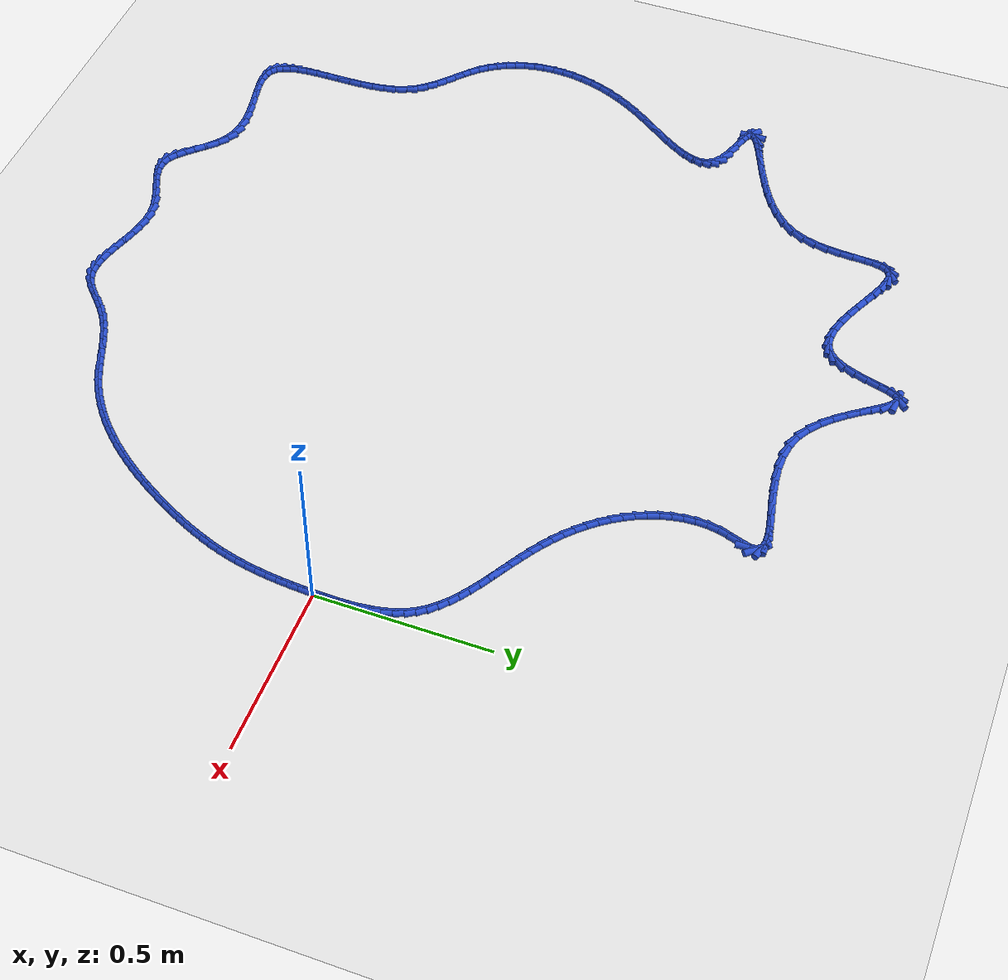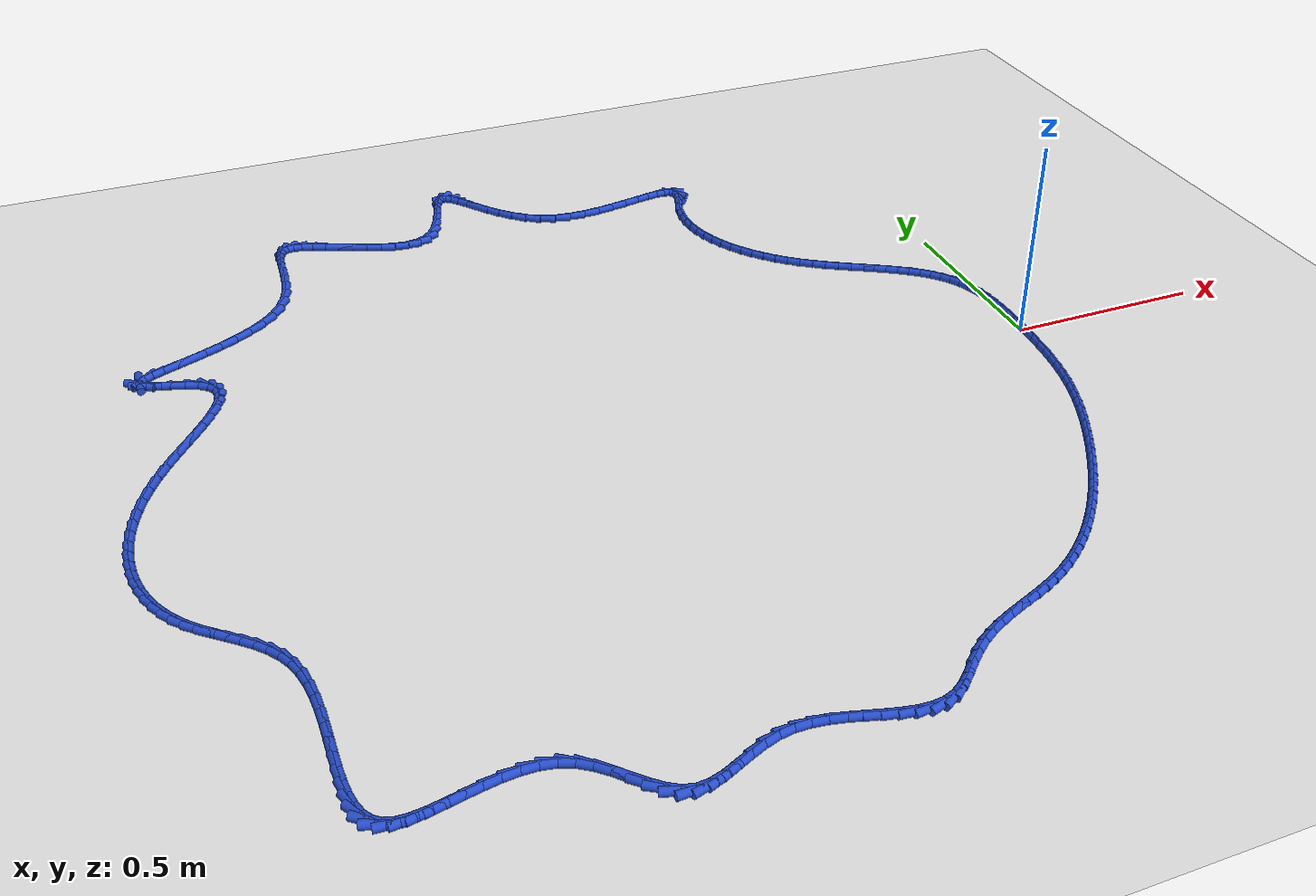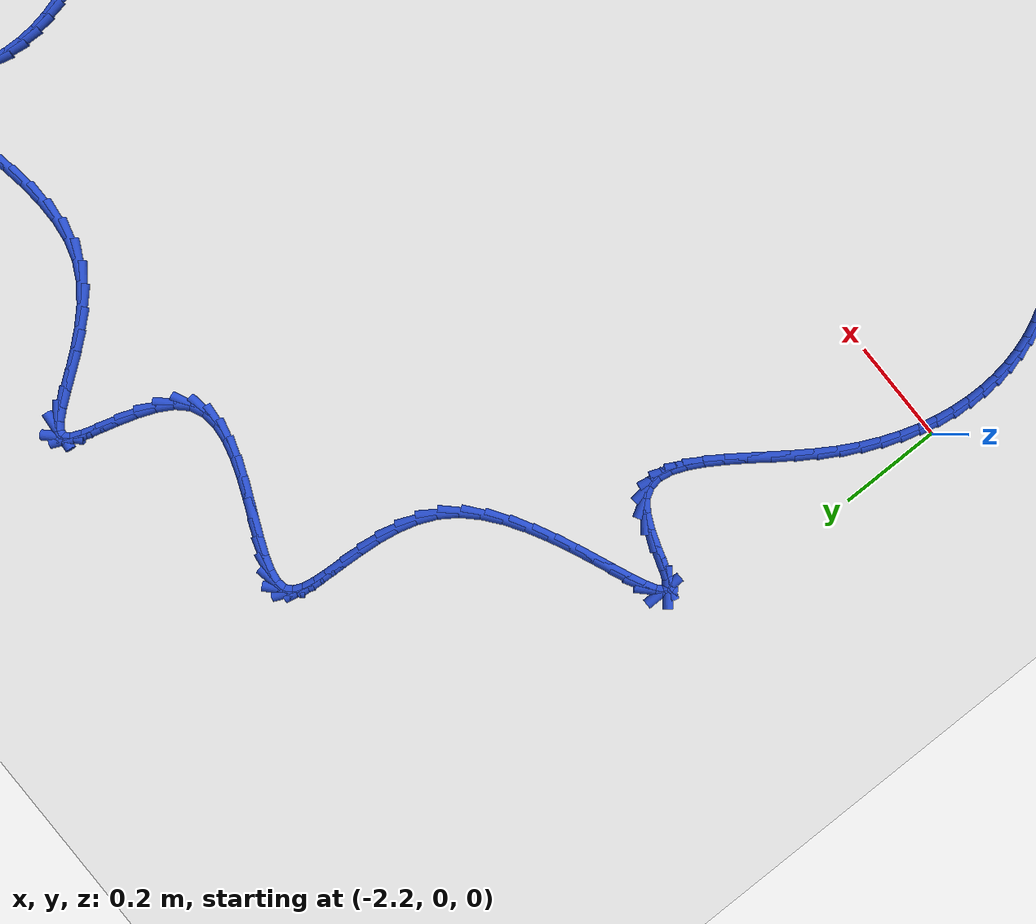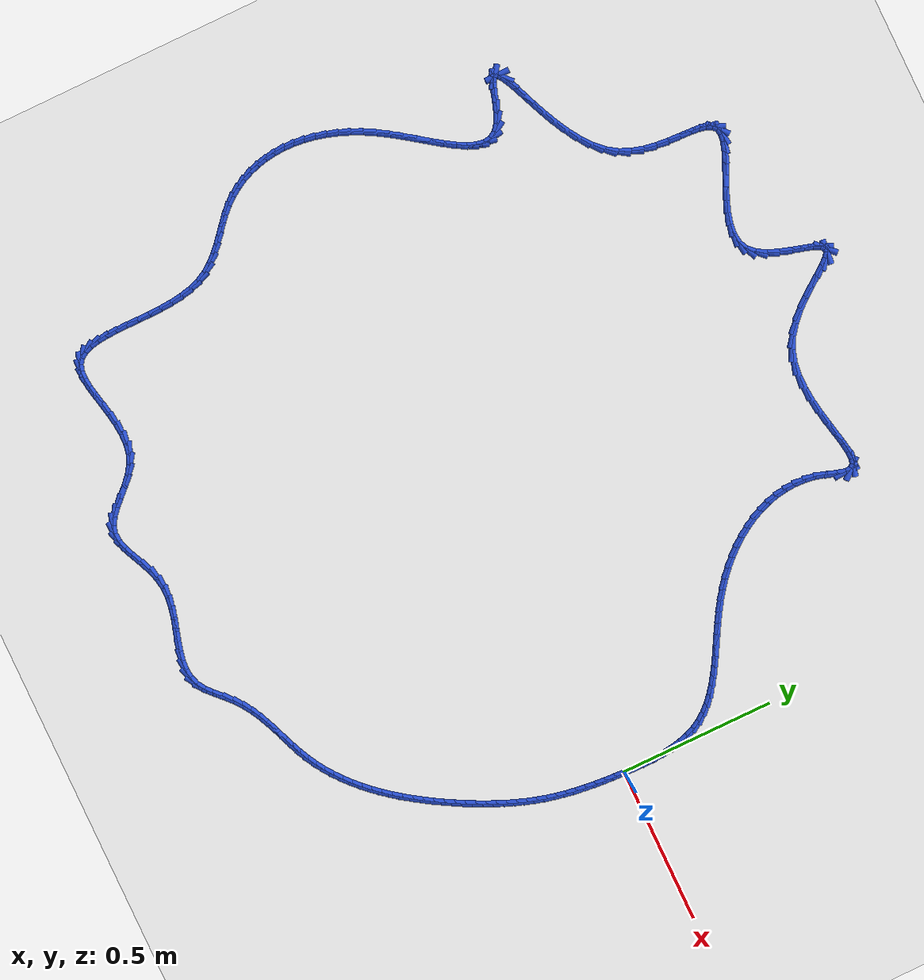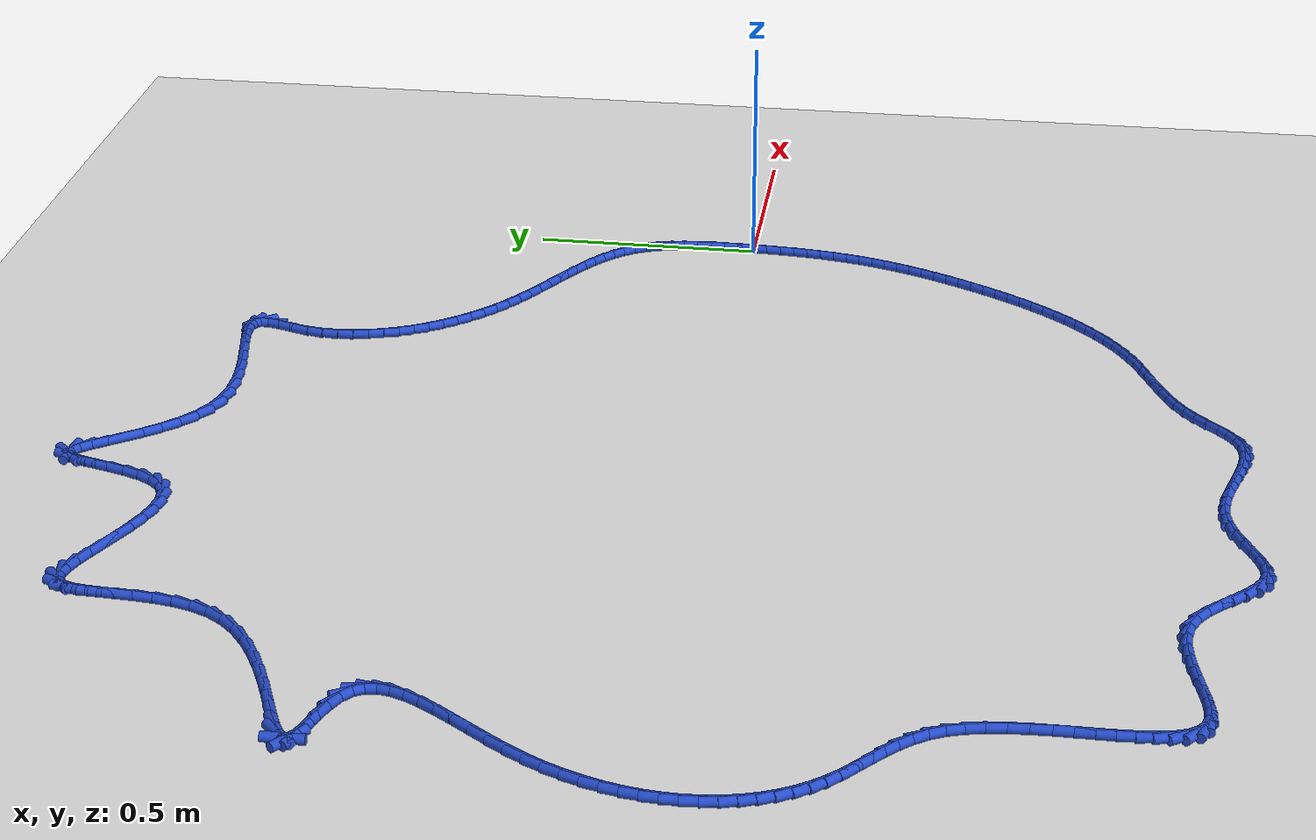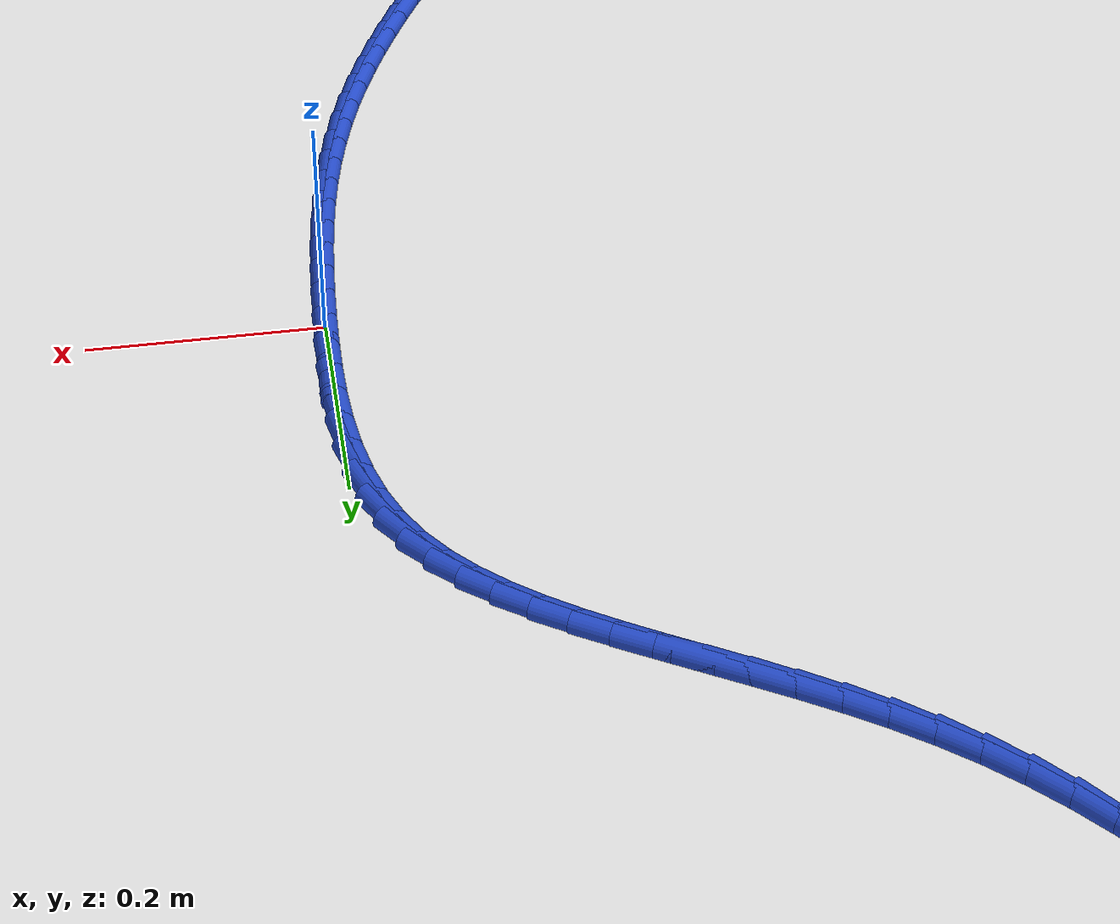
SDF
<sdf version="1.6">
 <world name="default">
  <light name="sun" type="directional">
   <pose>0 0 10 0 -0 0</pose>
   <diffuse>0.8 0.8 0.8 1</diffuse>
   <specular>0.2 0.2 0.2 1</specular>
   <attenuation>
    <range>1000</range>
    <constant>0.9</constant>
    <linear>0.01</linear>
    <quadratic>0.001</quadratic>
   </attenuation>
   <direction>-0.5 0.1 -0.9</direction>
  </light>
  <model name="ground_plane">
   <static>1</static>
   <link name="link">
    <collision name="collision">
     <geometry><plane><normal>0 0 1</normal><size>100 100</size></plane></geometry>
     <surface><friction><ode><mu>100</mu><mu2>50</mu2></ode></friction></surface>
    </collision>
    <visual name="visual">
     <cast_shadows>0</cast_shadows>
     <geometry><plane><normal>0 0 1</normal><size>100 100</size></plane></geometry>
     <material>
      <script><uri>file://media/materials/scripts/gazebo.material</uri><name>Gazebo/WhiteGlow</name></script>
     </material>
    </visual>
   </link>
  </model>
  <gravity>0 0 -9.8</gravity>
  <magnetic_field>6e-06 2.3e-05 -4.2e-05</magnetic_field>
  <atmosphere type="adiabatic"/>
  <physics name="default_physics" default="0" type="ode">
   <max_step_size>0.001</max_step_size>
   <real_time_factor>1</real_time_factor>
   <real_time_update_rate>1000</real_time_update_rate>
  </physics>
  <scene><ambient>0.4 0.4 0.4 1</ambient><background>0.7 0.7 0.7 1</background><shadows>1</shadows></scene>
  <spherical_coordinates>
   <surface_model>EARTH_WGS84</surface_model>
   <latitude_deg>0</latitude_deg>
   <longitude_deg>0</longitude_deg>
   <elevation>0</elevation>
   <heading_deg>0</heading_deg>
  </spherical_coordinates>
  <model name="line">
   <link name="link_0">
    <pose>-3.9871534893154426e-17 -2.0816681711721685e-17 0.01 0 1.57 1.538342685505387</pose>
    <collision name="collision">
     <geometry><cylinder><radius>0.01</radius><length>0.08</length></cylinder></geometry>
    </collision>
    <visual name="visual">
     <material>
      <script><name>Gazebo/Blue</name><uri>file://media/materials/scripts/gazebo.material</uri></script>
     </material>
     <geometry><cylinder><radius>0.01</radius><length>0.08</length></cylinder></geometry>
    </visual>
   </link>
   <link name="link_1">
    <pose>0.001082015016165012 0.03332862116855559 0.01 0 1.57 1.56089797634101</pose>
    <collision name="collision">
     <geometry><cylinder><radius>0.01</radius><length>0.08</length></cylinder></geometry>
    </collision>
    <visual name="visual">
     <material>
      <script><name>Gazebo/Blue</name><uri>file://media/materials/scripts/gazebo.material</uri></script>
     </material>
     <geometry><cylinder><radius>0.01</radius><length>0.08</length></cylinder></geometry>
    </visual>
   </link>
   <link name="link_2">
    <pose>0.0014136496515058847 0.0668315574327073 0.01 0 1.57 -1.5482920272042044</pose>
    <collision name="collision">
     <geometry><cylinder><radius>0.01</radius><length>0.08</length></cylinder></geometry>
    </collision>
    <visual name="visual">
     <material>
      <script><name>Gazebo/Blue</name><uri>file://media/materials/scripts/gazebo.material</uri></script>
     </material>
     <geometry><cylinder><radius>0.01</radius><length>0.08</length></cylinder></geometry>
    </visual>
   </link>
   <link name="link_3">
    <pose>0.0006632824911710362 0.10016920831925602 0.01 0 1.57 -1.504982040066577</pose>
    <collision name="collision">
     <geometry><cylinder><radius>0.01</radius><length>0.08</length></cylinder></geometry>
    </collision>
    <visual name="visual">
     <material>
      <script><name>Gazebo/Blue</name><uri>file://media/materials/scripts/gazebo.material</uri></script>
     </material>
     <geometry><cylinder><radius>0.01</radius><length>0.08</length></cylinder></geometry>
    </visual>
   </link>
   <link name="link_4">
    <pose>-0.0015007078796910735 0.13300197335500274 0.01 0 1.57 -1.449190964346713</pose>
    <collision name="collision">
     <geometry><cylinder><radius>0.01</radius><length>0.08</length></cylinder></geometry>
    </collision>
    <visual name="visual">
     <material>
      <script><name>Gazebo/Blue</name><uri>file://media/materials/scripts/gazebo.material</uri></script>
     </material>
     <geometry><cylinder><radius>0.01</radius><length>0.08</length></cylinder></geometry>
    </visual>
   </link>
   <link name="link_5">
    <pose>-0.005409942875931985 0.1649902520667484 0.01 0 1.57 -1.3788610137995028</pose>
    <collision name="collision">
     <geometry><cylinder><radius>0.01</radius><length>0.08</length></cylinder></geometry>
    </collision>
    <visual name="visual">
     <material>
      <script><name>Gazebo/Blue</name><uri>file://media/materials/scripts/gazebo.material</uri></script>
     </material>
     <geometry><cylinder><radius>0.01</radius><length>0.08</length></cylinder></geometry>
    </visual>
   </link>
   <link name="link_6">
    <pose>-0.011396043912403248 0.1957944439812939 0.01 0 1.57 -1.2915897562219265</pose>
    <collision name="collision">
     <geometry><cylinder><radius>0.01</radius><length>0.08</length></cylinder></geometry>
    </collision>
    <visual name="visual">
     <material>
      <script><name>Gazebo/Blue</name><uri>file://media/materials/scripts/gazebo.material</uri></script>
     </material>
     <geometry><cylinder><radius>0.01</radius><length>0.08</length></cylinder></geometry>
    </visual>
   </link>
   <link name="link_7">
    <pose>-0.019790632403956395 0.22507494862544022 0.01 0 1.57 -1.18502470711433</pose>
    <collision name="collision">
     <geometry><cylinder><radius>0.01</radius><length>0.08</length></cylinder></geometry>
    </collision>
    <visual name="visual">
     <material>
      <script><name>Gazebo/Blue</name><uri>file://media/materials/scripts/gazebo.material</uri></script>
     </material>
     <geometry><cylinder><radius>0.01</radius><length>0.08</length></cylinder></geometry>
    </visual>
   </link>
   <link name="link_8">
    <pose>-0.030925329765442967 0.25249216552598824 0.01 0 1.57 -1.0598615610531572</pose>
    <collision name="collision">
     <geometry><cylinder><radius>0.01</radius><length>0.08</length></cylinder></geometry>
    </collision>
    <visual name="visual">
     <material>
      <script><name>Gazebo/Blue</name><uri>file://media/materials/scripts/gazebo.material</uri></script>
     </material>
     <geometry><cylinder><radius>0.01</radius><length>0.08</length></cylinder></geometry>
    </visual>
   </link>
   <link name="link_9">
    <pose>-0.045085360770730214 0.27775147626223073 0.01 0 1.57 -0.9360327810155468</pose>
    <collision name="collision">
     <geometry><cylinder><radius>0.01</radius><length>0.08</length></cylinder></geometry>
    </collision>
    <visual name="visual">
     <material>
      <script><name>Gazebo/Blue</name><uri>file://media/materials/scripts/gazebo.material</uri></script>
     </material>
     <geometry><cylinder><radius>0.01</radius><length>0.08</length></cylinder></geometry>
    </visual>
   </link>
   <link name="link_10">
    <pose>-0.062162218842410674 0.30093998927848675 0.01 0 1.57 -0.8270121124530095</pose>
    <collision name="collision">
     <geometry><cylinder><radius>0.01</radius><length>0.08</length></cylinder></geometry>
    </collision>
    <visual name="visual">
     <material>
      <script><name>Gazebo/Blue</name><uri>file://media/materials/scripts/gazebo.material</uri></script>
     </material>
     <geometry><cylinder><radius>0.01</radius><length>0.08</length></cylinder></geometry>
    </visual>
   </link>
   <link name="link_11">
    <pose>-0.08184886702131684 0.3223372904024393 0.01 0 1.57 -0.7352734472264888</pose>
    <collision name="collision">
     <geometry><cylinder><radius>0.01</radius><length>0.08</length></cylinder></geometry>
    </collision>
    <visual name="visual">
     <material>
      <script><name>Gazebo/Blue</name><uri>file://media/materials/scripts/gazebo.material</uri></script>
     </material>
     <geometry><cylinder><radius>0.01</radius><length>0.08</length></cylinder></geometry>
    </visual>
   </link>
   <link name="link_12">
    <pose>-0.10383674887410213 0.34222443860865975 0.01 0 1.57 -0.6612122491124037</pose>
    <collision name="collision">
     <geometry><cylinder><radius>0.01</radius><length>0.08</length></cylinder></geometry>
    </collision>
    <visual name="visual">
     <material>
      <script><name>Gazebo/Blue</name><uri>file://media/materials/scripts/gazebo.material</uri></script>
     </material>
     <geometry><cylinder><radius>0.01</radius><length>0.08</length></cylinder></geometry>
    </visual>
   </link>
   <link name="link_13">
    <pose>-0.12781730796741975 0.36088249287171925 0.01 0 1.57 -0.604019672935559</pose>
    <collision name="collision">
     <geometry><cylinder><radius>0.01</radius><length>0.08</length></cylinder></geometry>
    </collision>
    <visual name="visual">
     <material>
      <script><name>Gazebo/Blue</name><uri>file://media/materials/scripts/gazebo.material</uri></script>
     </material>
     <geometry><cylinder><radius>0.01</radius><length>0.08</length></cylinder></geometry>
    </visual>
   </link>
   <link name="link_14">
    <pose>-0.15348198786792308 0.3785925121661891 0.01 0 1.57 -0.562390289282589</pose>
    <collision name="collision">
     <geometry><cylinder><radius>0.01</radius><length>0.08</length></cylinder></geometry>
    </collision>
    <visual name="visual">
     <material>
      <script><name>Gazebo/Blue</name><uri>file://media/materials/scripts/gazebo.material</uri></script>
     </material>
     <geometry><cylinder><radius>0.01</radius><length>0.08</length></cylinder></geometry>
    </visual>
   </link>
   <link name="link_15">
    <pose>-0.18052223214226554 0.3956355554666406 0.01 0 1.57 -0.5349807943799272</pose>
    <collision name="collision">
     <geometry><cylinder><radius>0.01</radius><length>0.08</length></cylinder></geometry>
    </collision>
    <visual name="visual">
     <material>
      <script><name>Gazebo/Blue</name><uri>file://media/materials/scripts/gazebo.material</uri></script>
     </material>
     <geometry><cylinder><radius>0.01</radius><length>0.08</length></cylinder></geometry>
    </visual>
   </link>
   <link name="link_16">
    <pose>-0.20862948435710033 0.41229268174764494 0.01 0 1.57 -0.5206485705988937</pose>
    <collision name="collision">
     <geometry><cylinder><radius>0.01</radius><length>0.08</length></cylinder></geometry>
    </collision>
    <visual name="visual">
     <material>
      <script><name>Gazebo/Blue</name><uri>file://media/materials/scripts/gazebo.material</uri></script>
     </material>
     <geometry><cylinder><radius>0.01</radius><length>0.08</length></cylinder></geometry>
    </visual>
   </link>
   <link name="link_17">
    <pose>-0.23749518807908096 0.4288449499837735 0.01 0 1.57 -0.5185467126453396</pose>
    <collision name="collision">
     <geometry><cylinder><radius>0.01</radius><length>0.08</length></cylinder></geometry>
    </collision>
    <visual name="visual">
     <material>
      <script><name>Gazebo/Blue</name><uri>file://media/materials/scripts/gazebo.material</uri></script>
     </material>
     <geometry><cylinder><radius>0.01</radius><length>0.08</length></cylinder></geometry>
    </visual>
   </link>
   <link name="link_18">
    <pose>-0.2668107868748606 0.4455734191495972 0.01 0 1.57 -0.5281381627532674</pose>
    <collision name="collision">
     <geometry><cylinder><radius>0.01</radius><length>0.08</length></cylinder></geometry>
    </collision>
    <visual name="visual">
     <material>
      <script><name>Gazebo/Blue</name><uri>file://media/materials/scripts/gazebo.material</uri></script>
     </material>
     <geometry><cylinder><radius>0.01</radius><length>0.08</length></cylinder></geometry>
    </visual>
   </link>
   <link name="link_19">
    <pose>-0.29626772431109266 0.46275914821968755 0.01 0 1.57 -0.5491650285958551</pose>
    <collision name="collision">
     <geometry><cylinder><radius>0.01</radius><length>0.08</length></cylinder></geometry>
    </collision>
    <visual name="visual">
     <material>
      <script><name>Gazebo/Blue</name><uri>file://media/materials/scripts/gazebo.material</uri></script>
     </material>
     <geometry><cylinder><radius>0.01</radius><length>0.08</length></cylinder></geometry>
    </visual>
   </link>
   <link name="link_20">
    <pose>-0.3255574439544306 0.48068319616861577 0.01 0 1.57 -0.5815873304614774</pose>
    <collision name="collision">
     <geometry><cylinder><radius>0.01</radius><length>0.08</length></cylinder></geometry>
    </collision>
    <visual name="visual">
     <material>
      <script><name>Gazebo/Blue</name><uri>file://media/materials/scripts/gazebo.material</uri></script>
     </material>
     <geometry><cylinder><radius>0.01</radius><length>0.08</length></cylinder></geometry>
    </visual>
   </link>
   <link name="link_21">
    <pose>-0.3543713893715276 0.49962662197095314 0.01 0 1.57 -0.625490948118242</pose>
    <collision name="collision">
     <geometry><cylinder><radius>0.01</radius><length>0.08</length></cylinder></geometry>
    </collision>
    <visual name="visual">
     <material>
      <script><name>Gazebo/Blue</name><uri>file://media/materials/scripts/gazebo.material</uri></script>
     </material>
     <geometry><cylinder><radius>0.01</radius><length>0.08</length></cylinder></geometry>
    </visual>
   </link>
   <link name="link_22">
    <pose>-0.3824010041290371 0.5198704846012708 0.01 0 1.57 -0.6798382243512482</pose>
    <collision name="collision">
     <geometry><cylinder><radius>0.01</radius><length>0.08</length></cylinder></geometry>
    </collision>
    <visual name="visual">
     <material>
      <script><name>Gazebo/Blue</name><uri>file://media/materials/scripts/gazebo.material</uri></script>
     </material>
     <geometry><cylinder><radius>0.01</radius><length>0.08</length></cylinder></geometry>
    </visual>
   </link>
   <link name="link_23">
    <pose>-0.4093498584260099 0.5416557725183224 0.01 0 1.57 -0.7378180528720488</pose>
    <collision name="collision">
     <geometry><cylinder><radius>0.01</radius><length>0.08</length></cylinder></geometry>
    </collision>
    <visual name="visual">
     <material>
      <script><name>Gazebo/Blue</name><uri>file://media/materials/scripts/gazebo.material</uri></script>
     </material>
     <geometry><cylinder><radius>0.01</radius><length>0.08</length></cylinder></geometry>
    </visual>
   </link>
   <link name="link_24">
    <pose>-0.43499761108740936 0.5649720514949751 0.01 0 1.57 -0.7973371385059201</pose>
    <collision name="collision">
     <geometry><cylinder><radius>0.01</radius><length>0.08</length></cylinder></geometry>
    </collision>
    <visual name="visual">
     <material>
      <script><name>Gazebo/Blue</name><uri>file://media/materials/scripts/gazebo.material</uri></script>
     </material>
     <geometry><cylinder><radius>0.01</radius><length>0.08</length></cylinder></geometry>
    </visual>
   </link>
   <link name="link_25">
    <pose>-0.4591533652901688 0.5897115931557524 0.01 0 1.57 -0.8590767394758316</pose>
    <collision name="collision">
     <geometry><cylinder><radius>0.01</radius><length>0.08</length></cylinder></geometry>
    </collision>
    <visual name="visual">
     <material>
      <script><name>Gazebo/Blue</name><uri>file://media/materials/scripts/gazebo.material</uri></script>
     </material>
     <geometry><cylinder><radius>0.01</radius><length>0.08</length></cylinder></geometry>
    </visual>
   </link>
   <link name="link_26">
    <pose>-0.48162628806213337 0.6157664581400633 0.01 0 1.57 -0.9237231046081564</pose>
    <collision name="collision">
     <geometry><cylinder><radius>0.01</radius><length>0.08</length></cylinder></geometry>
    </collision>
    <visual name="visual">
     <material>
      <script><name>Gazebo/Blue</name><uri>file://media/materials/scripts/gazebo.material</uri></script>
     </material>
     <geometry><cylinder><radius>0.01</radius><length>0.08</length></cylinder></geometry>
    </visual>
   </link>
   <link name="link_27">
    <pose>-0.5022255464311478 0.6430287070873159 0.01 0 1.57 -0.991954841910093</pose>
    <collision name="collision">
     <geometry><cylinder><radius>0.01</radius><length>0.08</length></cylinder></geometry>
    </collision>
    <visual name="visual">
     <material>
      <script><name>Gazebo/Blue</name><uri>file://media/materials/scripts/gazebo.material</uri></script>
     </material>
     <geometry><cylinder><radius>0.01</radius><length>0.08</length></cylinder></geometry>
    </visual>
   </link>
   <link name="link_28">
    <pose>-0.5207603074250569 0.6713904006369186 0.01 0 1.57 -1.0644244878383975</pose>
    <collision name="collision">
     <geometry><cylinder><radius>0.01</radius><length>0.08</length></cylinder></geometry>
    </collision>
    <visual name="visual">
     <material>
      <script><name>Gazebo/Blue</name><uri>file://media/materials/scripts/gazebo.material</uri></script>
     </material>
     <geometry><cylinder><radius>0.01</radius><length>0.08</length></cylinder></geometry>
    </visual>
   </link>
   <link name="link_29">
    <pose>-0.5370397380717057 0.7007435994282799 0.01 0 1.57 -1.1417243668034234</pose>
    <collision name="collision">
     <geometry><cylinder><radius>0.01</radius><length>0.08</length></cylinder></geometry>
    </collision>
    <visual name="visual">
     <material>
      <script><name>Gazebo/Blue</name><uri>file://media/materials/scripts/gazebo.material</uri></script>
     </material>
     <geometry><cylinder><radius>0.01</radius><length>0.08</length></cylinder></geometry>
    </visual>
   </link>
   <link name="link_30">
    <pose>-0.5508730053989387 0.7309803641008082 0.01 0 1.57 -1.2243329999260273</pose>
    <collision name="collision">
     <geometry><cylinder><radius>0.01</radius><length>0.08</length></cylinder></geometry>
    </collision>
    <visual name="visual">
     <material>
      <script><name>Gazebo/Blue</name><uri>file://media/materials/scripts/gazebo.material</uri></script>
     </material>
     <geometry><cylinder><radius>0.01</radius><length>0.08</length></cylinder></geometry>
    </visual>
   </link>
   <link name="link_31">
    <pose>-0.5620692764346011 0.7619927552939117 0.01 0 1.57 -1.3125405901365217</pose>
    <collision name="collision">
     <geometry><cylinder><radius>0.01</radius><length>0.08</length></cylinder></geometry>
    </collision>
    <visual name="visual">
     <material>
      <script><name>Gazebo/Blue</name><uri>file://media/materials/scripts/gazebo.material</uri></script>
     </material>
     <geometry><cylinder><radius>0.01</radius><length>0.08</length></cylinder></geometry>
    </visual>
   </link>
   <link name="link_32">
    <pose>-0.5704377182065375 0.7936728336469991 0.01 0 1.57 -1.406357694199434</pose>
    <collision name="collision">
     <geometry><cylinder><radius>0.01</radius><length>0.08</length></cylinder></geometry>
    </collision>
    <visual name="visual">
     <material>
      <script><name>Gazebo/Blue</name><uri>file://media/materials/scripts/gazebo.material</uri></script>
     </material>
     <geometry><cylinder><radius>0.01</radius><length>0.08</length></cylinder></geometry>
    </visual>
   </link>
   <link name="link_33">
    <pose>-0.5757874977425932 0.8259126597994789 0.01 0 1.57 -1.5054207553811982</pose>
    <collision name="collision">
     <geometry><cylinder><radius>0.01</radius><length>0.08</length></cylinder></geometry>
    </collision>
    <visual name="visual">
     <material>
      <script><name>Gazebo/Blue</name><uri>file://media/materials/scripts/gazebo.material</uri></script>
     </material>
     <geometry><cylinder><radius>0.01</radius><length>0.08</length></cylinder></geometry>
    </visual>
   </link>
   <link name="link_34">
    <pose>-0.5779277820706122 0.8586042943907588 0.01 0 1.57 1.5326726961803558</pose>
    <collision name="collision">
     <geometry><cylinder><radius>0.01</radius><length>0.08</length></cylinder></geometry>
    </collision>
    <visual name="visual">
     <material>
      <script><name>Gazebo/Blue</name><uri>file://media/materials/scripts/gazebo.material</uri></script>
     </material>
     <geometry><cylinder><radius>0.01</radius><length>0.08</length></cylinder></geometry>
    </visual>
   </link>
   <link name="link_35">
    <pose>-0.57666773821844 0.8916397980602478 0.01 0 1.57 1.4260096984658304</pose>
    <collision name="collision">
     <geometry><cylinder><radius>0.01</radius><length>0.08</length></cylinder></geometry>
    </collision>
    <visual name="visual">
     <material>
      <script><name>Gazebo/Blue</name><uri>file://media/materials/scripts/gazebo.material</uri></script>
     </material>
     <geometry><cylinder><radius>0.01</radius><length>0.08</length></cylinder></geometry>
    </visual>
   </link>
   <link name="link_36">
    <pose>-0.5718165332139213 0.9249112314473542 0.01 0 1.57 1.3178987571737524</pose>
    <collision name="collision">
     <geometry><cylinder><radius>0.01</radius><length>0.08</length></cylinder></geometry>
    </collision>
    <visual name="visual">
     <material>
      <script><name>Gazebo/Blue</name><uri>file://media/materials/scripts/gazebo.material</uri></script>
     </material>
     <geometry><cylinder><radius>0.01</radius><length>0.08</length></cylinder></geometry>
    </visual>
   </link>
   <link name="link_37">
    <pose>-0.5631854430144275 0.9583093147125279 0.01 0 1.57 1.2435623258044026</pose>
    <collision name="collision">
     <geometry><cylinder><radius>0.01</radius><length>0.08</length></cylinder></geometry>
    </collision>
    <visual name="visual">
     <material>
      <script><name>Gazebo/Blue</name><uri>file://media/materials/scripts/gazebo.material</uri></script>
     </material>
     <geometry><cylinder><radius>0.01</radius><length>0.08</length></cylinder></geometry>
    </visual>
   </link>
   <link name="link_38">
    <pose>-0.5521888733167679 0.9907057857998683 0.01 0 1.57 1.3042515144942324</pose>
    <collision name="collision">
     <geometry><cylinder><radius>0.01</radius><length>0.08</length></cylinder></geometry>
    </collision>
    <visual name="visual">
     <material>
      <script><name>Gazebo/Blue</name><uri>file://media/materials/scripts/gazebo.material</uri></script>
     </material>
     <geometry><cylinder><radius>0.01</radius><length>0.08</length></cylinder></geometry>
    </visual>
   </link>
   <link name="link_39">
    <pose>-0.5446983635642249 1.0181393463159147 0.01 0 1.57 -1.5069700538517636</pose>
    <collision name="collision">
     <geometry><cylinder><radius>0.01</radius><length>0.08</length></cylinder></geometry>
    </collision>
    <visual name="visual">
     <material>
      <script><name>Gazebo/Blue</name><uri>file://media/materials/scripts/gazebo.material</uri></script>
     </material>
     <geometry><cylinder><radius>0.01</radius><length>0.08</length></cylinder></geometry>
    </visual>
   </link>
   <link name="link_40">
    <pose>-0.5459192541731175 1.0372417036522428 0.01 0 1.57 -0.8416801528754385</pose>
    <collision name="collision">
     <geometry><cylinder><radius>0.01</radius><length>0.08</length></cylinder></geometry>
    </collision>
    <visual name="visual">
     <material>
      <script><name>Gazebo/Blue</name><uri>file://media/materials/scripts/gazebo.material</uri></script>
     </material>
     <geometry><cylinder><radius>0.01</radius><length>0.08</length></cylinder></geometry>
    </visual>
   </link>
   <link name="link_41">
    <pose>-0.5559627871671851 1.0484845426080276 0.01 0 1.57 -0.25786241157151585</pose>
    <collision name="collision">
     <geometry><cylinder><radius>0.01</radius><length>0.08</length></cylinder></geometry>
    </collision>
    <visual name="visual">
     <material>
      <script><name>Gazebo/Blue</name><uri>file://media/materials/scripts/gazebo.material</uri></script>
     </material>
     <geometry><cylinder><radius>0.01</radius><length>0.08</length></cylinder></geometry>
    </visual>
   </link>
   <link name="link_42">
    <pose>-0.5738100465247395 1.0531914713311903 0.01 0 1.57 0.02051400773669302</pose>
    <collision name="collision">
     <geometry><cylinder><radius>0.01</radius><length>0.08</length></cylinder></geometry>
    </collision>
    <visual name="visual">
     <material>
      <script><name>Gazebo/Blue</name><uri>file://media/materials/scripts/gazebo.material</uri></script>
     </material>
     <geometry><cylinder><radius>0.01</radius><length>0.08</length></cylinder></geometry>
    </visual>
   </link>
   <link name="link_43">
    <pose>-0.5984421162240932 1.0526860979696517 0.01 0 1.57 0.14355700047401923</pose>
    <collision name="collision">
     <geometry><cylinder><radius>0.01</radius><length>0.08</length></cylinder></geometry>
    </collision>
    <visual name="visual">
     <material>
      <script><name>Gazebo/Blue</name><uri>file://media/materials/scripts/gazebo.material</uri></script>
     </material>
     <geometry><cylinder><radius>0.01</radius><length>0.08</length></cylinder></geometry>
    </visual>
   </link>
   <link name="link_44">
    <pose>-0.6288400802435582 1.0482920306713335 0.01 0 1.57 0.19548418985887223</pose>
    <collision name="collision">
     <geometry><cylinder><radius>0.01</radius><length>0.08</length></cylinder></geometry>
    </collision>
    <visual name="visual">
     <material>
      <script><name>Gazebo/Blue</name><uri>file://media/materials/scripts/gazebo.material</uri></script>
     </material>
     <geometry><cylinder><radius>0.01</radius><length>0.08</length></cylinder></geometry>
    </visual>
   </link>
   <link name="link_45">
    <pose>-0.6639850225614471 1.0413328775841566 0.01 0 1.57 0.20791101739568002</pose>
    <collision name="collision">
     <geometry><cylinder><radius>0.01</radius><length>0.08</length></cylinder></geometry>
    </collision>
    <visual name="visual">
     <material>
      <script><name>Gazebo/Blue</name><uri>file://media/materials/scripts/gazebo.material</uri></script>
     </material>
     <geometry><cylinder><radius>0.01</radius><length>0.08</length></cylinder></geometry>
    </visual>
   </link>
   <link name="link_46">
    <pose>-0.7028580271560715 1.0331322468560424 0.01 0 1.57 0.19281450056939628</pose>
    <collision name="collision">
     <geometry><cylinder><radius>0.01</radius><length>0.08</length></cylinder></geometry>
    </collision>
    <visual name="visual">
     <material>
      <script><name>Gazebo/Blue</name><uri>file://media/materials/scripts/gazebo.material</uri></script>
     </material>
     <geometry><cylinder><radius>0.01</radius><length>0.08</length></cylinder></geometry>
    </visual>
   </link>
   <link name="link_47">
    <pose>-0.7444401780057441 1.0250137466349114 0.01 0 1.57 0.1539013766421355</pose>
    <collision name="collision">
     <geometry><cylinder><radius>0.01</radius><length>0.08</length></cylinder></geometry>
    </collision>
    <visual name="visual">
     <material>
      <script><name>Gazebo/Blue</name><uri>file://media/materials/scripts/gazebo.material</uri></script>
     </material>
     <geometry><cylinder><radius>0.01</radius><length>0.08</length></cylinder></geometry>
    </visual>
   </link>
   <link name="link_48">
    <pose>-0.787712559088777 1.0183009850686853 0.01 0 1.57 0.09040108089133105</pose>
    <collision name="collision">
     <geometry><cylinder><radius>0.01</radius><length>0.08</length></cylinder></geometry>
    </collision>
    <visual name="visual">
     <material>
      <script><name>Gazebo/Blue</name><uri>file://media/materials/scripts/gazebo.material</uri></script>
     </material>
     <geometry><cylinder><radius>0.01</radius><length>0.08</length></cylinder></geometry>
    </visual>
   </link>
   <link name="link_49">
    <pose>-0.8316562543834821 1.0143175703052851 0.01 0 1.57 -0.0015950999920103155</pose>
    <collision name="collision">
     <geometry><cylinder><radius>0.01</radius><length>0.08</length></cylinder></geometry>
    </collision>
    <visual name="visual">
     <material>
      <script><name>Gazebo/Blue</name><uri>file://media/materials/scripts/gazebo.material</uri></script>
     </material>
     <geometry><cylinder><radius>0.01</radius><length>0.08</length></cylinder></geometry>
    </visual>
   </link>
   <link name="link_50">
    <pose>-0.8752523478681721 1.0143871104926323 0.01 0 1.57 -0.12825628001047357</pose>
    <collision name="collision">
     <geometry><cylinder><radius>0.01</radius><length>0.08</length></cylinder></geometry>
    </collision>
    <visual name="visual">
     <material>
      <script><name>Gazebo/Blue</name><uri>file://media/materials/scripts/gazebo.material</uri></script>
     </material>
     <geometry><cylinder><radius>0.01</radius><length>0.08</length></cylinder></geometry>
    </visual>
   </link>
   <link name="link_51">
    <pose>-0.9174819235211589 1.0198332137786479 0.01 0 1.57 -0.2958955044156219</pose>
    <collision name="collision">
     <geometry><cylinder><radius>0.01</radius><length>0.08</length></cylinder></geometry>
    </collision>
    <visual name="visual">
     <material>
      <script><name>Gazebo/Blue</name><uri>file://media/materials/scripts/gazebo.material</uri></script>
     </material>
     <geometry><cylinder><radius>0.01</radius><length>0.08</length></cylinder></geometry>
    </visual>
   </link>
   <link name="link_52">
    <pose>-0.9573260653207549 1.0319794883112527 0.01 0 1.57 -0.4928797768121747</pose>
    <collision name="collision">
     <geometry><cylinder><radius>0.01</radius><length>0.08</length></cylinder></geometry>
    </collision>
    <visual name="visual">
     <material>
      <script><name>Gazebo/Blue</name><uri>file://media/materials/scripts/gazebo.material</uri></script>
     </material>
     <geometry><cylinder><radius>0.01</radius><length>0.08</length></cylinder></geometry>
    </visual>
   </link>
   <link name="link_53">
    <pose>-0.9939422205457629 1.0516457663799597 0.01 0 1.57 -0.6581254125900383</pose>
    <collision name="collision">
     <geometry><cylinder><radius>0.01</radius><length>0.08</length></cylinder></geometry>
    </collision>
    <visual name="visual">
     <material>
      <script><name>Gazebo/Blue</name><uri>file://media/materials/scripts/gazebo.material</uri></script>
     </material>
     <geometry><cylinder><radius>0.01</radius><length>0.08</length></cylinder></geometry>
    </visual>
   </link>
   <link name="link_54">
    <pose>-1.0272716527477728 1.0774129353545727 0.01 0 1.57 -0.7791599914562944</pose>
    <collision name="collision">
     <geometry><cylinder><radius>0.01</radius><length>0.08</length></cylinder></geometry>
    </collision>
    <visual name="visual">
     <material>
      <script><name>Gazebo/Blue</name><uri>file://media/materials/scripts/gazebo.material</uri></script>
     </material>
     <geometry><cylinder><radius>0.01</radius><length>0.08</length></cylinder></geometry>
    </visual>
   </link>
   <link name="link_55">
    <pose>-1.057473298693066 1.1072401063607482 0.01 0 1.57 -0.86332951874798</pose>
    <collision name="collision">
     <geometry><cylinder><radius>0.01</radius><length>0.08</length></cylinder></geometry>
    </collision>
    <visual name="visual">
     <material>
      <script><name>Gazebo/Blue</name><uri>file://media/materials/scripts/gazebo.material</uri></script>
     </material>
     <geometry><cylinder><radius>0.01</radius><length>0.08</length></cylinder></geometry>
    </visual>
   </link>
   <link name="link_56">
    <pose>-1.084706103627189 1.1390863663034132 0.01 0 1.57 -0.9162353490977402</pose>
    <collision name="collision">
     <geometry><cylinder><radius>0.01</radius><length>0.08</length></cylinder></geometry>
    </collision>
    <visual name="visual">
     <material>
      <script><name>Gazebo/Blue</name><uri>file://media/materials/scripts/gazebo.material</uri></script>
     </material>
     <geometry><cylinder><radius>0.01</radius><length>0.08</length></cylinder></geometry>
    </visual>
   </link>
   <link name="link_57">
    <pose>-1.1091290127956868 1.1709108020874945 0.01 0 1.57 -0.939212798556779</pose>
    <collision name="collision">
     <geometry><cylinder><radius>0.01</radius><length>0.08</length></cylinder></geometry>
    </collision>
    <visual name="visual">
     <material>
      <script><name>Gazebo/Blue</name><uri>file://media/materials/scripts/gazebo.material</uri></script>
     </material>
     <geometry><cylinder><radius>0.01</radius><length>0.08</length></cylinder></geometry>
    </visual>
   </link>
   <link name="link_58">
    <pose>-1.1309009714441047 1.2006725006179186 0.01 0 1.57 -0.9263874654811184</pose>
    <collision name="collision">
     <geometry><cylinder><radius>0.01</radius><length>0.08</length></cylinder></geometry>
    </collision>
    <visual name="visual">
     <material>
      <script><name>Gazebo/Blue</name><uri>file://media/materials/scripts/gazebo.material</uri></script>
     </material>
     <geometry><cylinder><radius>0.01</radius><length>0.08</length></cylinder></geometry>
    </visual>
   </link>
   <link name="link_59">
    <pose>-1.150180924817988 1.226330548799612 0.01 0 1.57 -0.8556762204629264</pose>
    <collision name="collision">
     <geometry><cylinder><radius>0.01</radius><length>0.08</length></cylinder></geometry>
    </collision>
    <visual name="visual">
     <material>
      <script><name>Gazebo/Blue</name><uri>file://media/materials/scripts/gazebo.material</uri></script>
     </material>
     <geometry><cylinder><radius>0.01</radius><length>0.08</length></cylinder></geometry>
    </visual>
   </link>
   <link name="link_60">
    <pose>-1.167127818162882 1.245844033537501 0.01 0 1.57 -0.6541769925117694</pose>
    <collision name="collision">
     <geometry><cylinder><radius>0.01</radius><length>0.08</length></cylinder></geometry>
    </collision>
    <visual name="visual">
     <material>
      <script><name>Gazebo/Blue</name><uri>file://media/materials/scripts/gazebo.material</uri></script>
     </material>
     <geometry><cylinder><radius>0.01</radius><length>0.08</length></cylinder></geometry>
    </visual>
   </link>
   <link name="link_61">
    <pose>-1.1819005967243323 1.2571720417365129 0.01 0 1.57 -0.08613626146449604</pose>
    <collision name="collision">
     <geometry><cylinder><radius>0.01</radius><length>0.08</length></cylinder></geometry>
    </collision>
    <visual name="visual">
     <material>
      <script><name>Gazebo/Blue</name><uri>file://media/materials/scripts/gazebo.material</uri></script>
     </material>
     <geometry><cylinder><radius>0.01</radius><length>0.08</length></cylinder></geometry>
    </visual>
   </link>
   <link name="link_62">
    <pose>-1.1946582057478843 1.258273660301574 0.01 0 1.57 0.7870718419445214</pose>
    <collision name="collision">
     <geometry><cylinder><radius>0.01</radius><length>0.08</length></cylinder></geometry>
    </collision>
    <visual name="visual">
     <material>
      <script><name>Gazebo/Blue</name><uri>file://media/materials/scripts/gazebo.material</uri></script>
     </material>
     <geometry><cylinder><radius>0.01</radius><length>0.08</length></cylinder></geometry>
    </visual>
   </link>
   <link name="link_63">
    <pose>-1.205588448902238 1.2473067683477272 0.01 0 1.57 1.1560351252224266</pose>
    <collision name="collision">
     <geometry><cylinder><radius>0.01</radius><length>0.08</length></cylinder></geometry>
    </collision>
    <visual name="visual">
     <material>
      <script><name>Gazebo/Blue</name><uri>file://media/materials/scripts/gazebo.material</uri></script>
     </material>
     <geometry><cylinder><radius>0.01</radius><length>0.08</length></cylinder></geometry>
    </visual>
   </link>
   <link name="link_64">
    <pose>-1.215291468842116 1.2252696558437115 0.01 0 1.57 1.2675442248159452</pose>
    <collision name="collision">
     <geometry><cylinder><radius>0.01</radius><length>0.08</length></cylinder></geometry>
    </collision>
    <visual name="visual">
     <material>
      <script><name>Gazebo/Blue</name><uri>file://media/materials/scripts/gazebo.material</uri></script>
     </material>
     <geometry><cylinder><radius>0.01</radius><length>0.08</length></cylinder></geometry>
    </visual>
   </link>
   <link name="link_65">
    <pose>-1.2246751560980838 1.1952805442621273 0.01 0 1.57 1.2913073765914385</pose>
    <collision name="collision">
     <geometry><cylinder><radius>0.01</radius><length>0.08</length></cylinder></geometry>
    </collision>
    <visual name="visual">
     <material>
      <script><name>Gazebo/Blue</name><uri>file://media/materials/scripts/gazebo.material</uri></script>
     </material>
     <geometry><cylinder><radius>0.01</radius><length>0.08</length></cylinder></geometry>
    </visual>
   </link>
   <link name="link_66">
    <pose>-1.2346547785162367 1.1605084739595897 0.01 0 1.57 1.2649046296979543</pose>
    <collision name="collision">
     <geometry><cylinder><radius>0.01</radius><length>0.08</length></cylinder></geometry>
    </collision>
    <visual name="visual">
     <material>
      <script><name>Gazebo/Blue</name><uri>file://media/materials/scripts/gazebo.material</uri></script>
     </material>
     <geometry><cylinder><radius>0.01</radius><length>0.08</length></cylinder></geometry>
    </visual>
   </link>
   <link name="link_67">
    <pose>-1.2461456039426702 1.124122485292715 0.01 0 1.57 1.1906625044714105</pose>
    <collision name="collision">
     <geometry><cylinder><radius>0.01</radius><length>0.08</length></cylinder></geometry>
    </collision>
    <visual name="visual">
     <material>
      <script><name>Gazebo/Blue</name><uri>file://media/materials/scripts/gazebo.material</uri></script>
     </material>
     <geometry><cylinder><radius>0.01</radius><length>0.08</length></cylinder></geometry>
    </visual>
   </link>
   <link name="link_68">
    <pose>-1.2600629002234807 1.0892916186181192 0.01 0 1.57 1.0502690449166987</pose>
    <collision name="collision">
     <geometry><cylinder><radius>0.01</radius><length>0.08</length></cylinder></geometry>
    </collision>
    <visual name="visual">
     <material>
      <script><name>Gazebo/Blue</name><uri>file://media/materials/scripts/gazebo.material</uri></script>
     </material>
     <geometry><cylinder><radius>0.01</radius><length>0.08</length></cylinder></geometry>
    </visual>
   </link>
   <link name="link_69">
    <pose>-1.277321935204764 1.0591849142924177 0.01 0 1.57 0.8014399627049505</pose>
    <collision name="collision">
     <geometry><cylinder><radius>0.01</radius><length>0.08</length></cylinder></geometry>
    </collision>
    <visual name="visual">
     <material>
      <script><name>Gazebo/Blue</name><uri>file://media/materials/scripts/gazebo.material</uri></script>
     </material>
     <geometry><cylinder><radius>0.01</radius><length>0.08</length></cylinder></geometry>
    </visual>
   </link>
   <link name="link_70">
    <pose>-1.2988368228725595 1.036968436655702 0.01 0 1.57 0.44089542119227426</pose>
    <collision name="collision">
     <geometry><cylinder><radius>0.01</radius><length>0.08</length></cylinder></geometry>
    </collision>
    <visual name="visual">
     <material>
      <script><name>Gazebo/Blue</name><uri>file://media/materials/scripts/gazebo.material</uri></script>
     </material>
     <geometry><cylinder><radius>0.01</radius><length>0.08</length></cylinder></geometry>
    </visual>
   </link>
   <link name="link_71">
    <pose>-1.3250524218235935 1.0245979544101391 0.01 0 1.57 0.11979422280806351</pose>
    <collision name="collision">
     <geometry><cylinder><radius>0.01</radius><length>0.08</length></cylinder></geometry>
    </collision>
    <visual name="visual">
     <material>
      <script><name>Gazebo/Blue</name><uri>file://media/materials/scripts/gazebo.material</uri></script>
     </material>
     <geometry><cylinder><radius>0.01</radius><length>0.08</length></cylinder></geometry>
    </visual>
   </link>
   <link name="link_72">
    <pose>-1.355225896711307 1.020965955938719 0.01 0 1.57 -0.10566894988549089</pose>
    <collision name="collision">
     <geometry><cylinder><radius>0.01</radius><length>0.08</length></cylinder></geometry>
    </collision>
    <visual name="visual">
     <material>
      <script><name>Gazebo/Blue</name><uri>file://media/materials/scripts/gazebo.material</uri></script>
     </material>
     <geometry><cylinder><radius>0.01</radius><length>0.08</length></cylinder></geometry>
    </visual>
   </link>
   <link name="link_73">
    <pose>-1.388429360946096 1.0244876485588335 0.01 0 1.57 -0.2520091974335301</pose>
    <collision name="collision">
     <geometry><cylinder><radius>0.01</radius><length>0.08</length></cylinder></geometry>
    </collision>
    <visual name="visual">
     <material>
      <script><name>Gazebo/Blue</name><uri>file://media/materials/scripts/gazebo.material</uri></script>
     </material>
     <geometry><cylinder><radius>0.01</radius><length>0.08</length></cylinder></geometry>
    </visual>
   </link>
   <link name="link_74">
    <pose>-1.423734927938358 1.0335782395878768 0.01 0 1.57 -0.3441467476202652</pose>
    <collision name="collision">
     <geometry><cylinder><radius>0.01</radius><length>0.08</length></cylinder></geometry>
    </collision>
    <visual name="visual">
     <material>
      <script><name>Gazebo/Blue</name><uri>file://media/materials/scripts/gazebo.material</uri></script>
     </material>
     <geometry><cylinder><radius>0.01</radius><length>0.08</length></cylinder></geometry>
    </visual>
   </link>
   <link name="link_75">
    <pose>-1.4602147110984887 1.0466529363432417 0.01 0 1.57 -0.3987625711534483</pose>
    <collision name="collision">
     <geometry><cylinder><radius>0.01</radius><length>0.08</length></cylinder></geometry>
    </collision>
    <visual name="visual">
     <material>
      <script><name>Gazebo/Blue</name><uri>file://media/materials/scripts/gazebo.material</uri></script>
     </material>
     <geometry><cylinder><radius>0.01</radius><length>0.08</length></cylinder></geometry>
    </visual>
   </link>
   <link name="link_76">
    <pose>-1.4969408238368855 1.0621269461423224 0.01 0 1.57 -0.42443273840732293</pose>
    <collision name="collision">
     <geometry><cylinder><radius>0.01</radius><length>0.08</length></cylinder></geometry>
    </collision>
    <visual name="visual">
     <material>
      <script><name>Gazebo/Blue</name><uri>file://media/materials/scripts/gazebo.material</uri></script>
     </material>
     <geometry><cylinder><radius>0.01</radius><length>0.08</length></cylinder></geometry>
    </visual>
   </link>
   <link name="link_77">
    <pose>-1.5329853795639452 1.0784154763025116 0.01 0 1.57 -0.4233961348781415</pose>
    <collision name="collision">
     <geometry><cylinder><radius>0.01</radius><length>0.08</length></cylinder></geometry>
    </collision>
    <visual name="visual">
     <material>
      <script><name>Gazebo/Blue</name><uri>file://media/materials/scripts/gazebo.material</uri></script>
     </material>
     <geometry><cylinder><radius>0.01</radius><length>0.08</length></cylinder></geometry>
    </visual>
   </link>
   <link name="link_78">
    <pose>-1.5674204916900643 1.0939337341412023 0.01 0 1.57 -0.3913791133021768</pose>
    <collision name="collision">
     <geometry><cylinder><radius>0.01</radius><length>0.08</length></cylinder></geometry>
    </collision>
    <visual name="visual">
     <material>
      <script><name>Gazebo/Blue</name><uri>file://media/materials/scripts/gazebo.material</uri></script>
     </material>
     <geometry><cylinder><radius>0.01</radius><length>0.08</length></cylinder></geometry>
    </visual>
   </link>
   <link name="link_79">
    <pose>-1.5993182736256393 1.1070969269757882 0.01 0 1.57 -0.31368310989898596</pose>
    <collision name="collision">
     <geometry><cylinder><radius>0.01</radius><length>0.08</length></cylinder></geometry>
    </collision>
    <visual name="visual">
     <material>
      <script><name>Gazebo/Blue</name><uri>file://media/materials/scripts/gazebo.material</uri></script>
     </material>
     <geometry><cylinder><radius>0.01</radius><length>0.08</length></cylinder></geometry>
    </visual>
   </link>
   <link name="link_80">
    <pose>-1.6277508387810669 1.1163202621236623 0.01 0 1.57 -0.15266176484688126</pose>
    <collision name="collision">
     <geometry><cylinder><radius>0.01</radius><length>0.08</length></cylinder></geometry>
    </collision>
    <visual name="visual">
     <material>
      <script><name>Gazebo/Blue</name><uri>file://media/materials/scripts/gazebo.material</uri></script>
     </material>
     <geometry><cylinder><radius>0.01</radius><length>0.08</length></cylinder></geometry>
    </visual>
   </link>
   <link name="link_81">
    <pose>-1.651790300566745 1.1200189469022184 0.01 0 1.57 0.18020241364457096</pose>
    <collision name="collision">
     <geometry><cylinder><radius>0.01</radius><length>0.08</length></cylinder></geometry>
    </collision>
    <visual name="visual">
     <material>
      <script><name>Gazebo/Blue</name><uri>file://media/materials/scripts/gazebo.material</uri></script>
     </material>
     <geometry><cylinder><radius>0.01</radius><length>0.08</length></cylinder></geometry>
    </visual>
   </link>
   <link name="link_82">
    <pose>-1.670509233972487 1.116608756830729 0.01 0 1.57 0.7251034351288039</pose>
    <collision name="collision">
     <geometry><cylinder><radius>0.01</radius><length>0.08</length></cylinder></geometry>
    </collision>
    <visual name="visual">
     <material>
      <script><name>Gazebo/Blue</name><uri>file://media/materials/scripts/gazebo.material</uri></script>
     </material>
     <geometry><cylinder><radius>0.01</radius><length>0.08</length></cylinder></geometry>
    </visual>
   </link>
   <link name="link_83">
    <pose>-1.6834772458432412 1.1051173110745312 0.01 0 1.57 1.1575720080335494</pose>
    <collision name="collision">
     <geometry><cylinder><radius>0.01</radius><length>0.08</length></cylinder></geometry>
    </collision>
    <visual name="visual">
     <material>
      <script><name>Gazebo/Blue</name><uri>file://media/materials/scripts/gazebo.material</uri></script>
     </material>
     <geometry><cylinder><radius>0.01</radius><length>0.08</length></cylinder></geometry>
    </visual>
   </link>
   <link name="link_84">
    <pose>-1.6917068388883099 1.086348426154164 0.01 0 1.57 1.3819173327217311</pose>
    <collision name="collision">
     <geometry><cylinder><radius>0.01</radius><length>0.08</length></cylinder></geometry>
    </collision>
    <visual name="visual">
     <material>
      <script><name>Gazebo/Blue</name><uri>file://media/materials/scripts/gazebo.material</uri></script>
     </material>
     <geometry><cylinder><radius>0.01</radius><length>0.08</length></cylinder></geometry>
    </visual>
   </link>
   <link name="link_85">
    <pose>-1.6964708712470897 1.0614264147796493 0.01 0 1.57 1.4851546041089552</pose>
    <collision name="collision">
     <geometry><cylinder><radius>0.01</radius><length>0.08</length></cylinder></geometry>
    </collision>
    <visual name="visual">
     <material>
      <script><name>Gazebo/Blue</name><uri>file://media/materials/scripts/gazebo.material</uri></script>
     </material>
     <geometry><cylinder><radius>0.01</radius><length>0.08</length></cylinder></geometry>
    </visual>
   </link>
   <link name="link_86">
    <pose>-1.699042201058977 1.031475589661009 0.01 0 1.57 1.522054296327508</pose>
    <collision name="collision">
     <geometry><cylinder><radius>0.01</radius><length>0.08</length></cylinder></geometry>
    </collision>
    <visual name="visual">
     <material>
      <script><name>Gazebo/Blue</name><uri>file://media/materials/scripts/gazebo.material</uri></script>
     </material>
     <geometry><cylinder><radius>0.01</radius><length>0.08</length></cylinder></geometry>
    </visual>
   </link>
   <link name="link_87">
    <pose>-1.7006936864633682 0.9976202635082653 0.01 0 1.57 1.5161361844266164</pose>
    <collision name="collision">
     <geometry><cylinder><radius>0.01</radius><length>0.08</length></cylinder></geometry>
    </collision>
    <visual name="visual">
     <material>
      <script><name>Gazebo/Blue</name><uri>file://media/materials/scripts/gazebo.material</uri></script>
     </material>
     <geometry><cylinder><radius>0.01</radius><length>0.08</length></cylinder></geometry>
    </visual>
   </link>
   <link name="link_88">
    <pose>-1.7026981855996597 0.9609847490314396 0.01 0 1.57 1.4762698084401473</pose>
    <collision name="collision">
     <geometry><cylinder><radius>0.01</radius><length>0.08</length></cylinder></geometry>
    </collision>
    <visual name="visual">
     <material>
      <script><name>Gazebo/Blue</name><uri>file://media/materials/scripts/gazebo.material</uri></script>
     </material>
     <geometry><cylinder><radius>0.01</radius><length>0.08</length></cylinder></geometry>
    </visual>
   </link>
   <link name="link_89">
    <pose>-1.7063285566072486 0.9226933589405543 0.01 0 1.57 1.4041791667592345</pose>
    <collision name="collision">
     <geometry><cylinder><radius>0.01</radius><length>0.08</length></cylinder></geometry>
    </collision>
    <visual name="visual">
     <material>
      <script><name>Gazebo/Blue</name><uri>file://media/materials/scripts/gazebo.material</uri></script>
     </material>
     <geometry><cylinder><radius>0.01</radius><length>0.08</length></cylinder></geometry>
    </visual>
   </link>
   <link name="link_90">
    <pose>-1.712857657625531 0.8838704059456312 0.01 0 1.57 1.2978790147797123</pose>
    <collision name="collision">
     <geometry><cylinder><radius>0.01</radius><length>0.08</length></cylinder></geometry>
    </collision>
    <visual name="visual">
     <material>
      <script><name>Gazebo/Blue</name><uri>file://media/materials/scripts/gazebo.material</uri></script>
     </material>
     <geometry><cylinder><radius>0.01</radius><length>0.08</length></cylinder></geometry>
    </visual>
   </link>
   <link name="link_91">
    <pose>-1.7235583467939035 0.8456402027566923 0.01 0 1.57 1.1544701277788771</pose>
    <collision name="collision">
     <geometry><cylinder><radius>0.01</radius><length>0.08</length></cylinder></geometry>
    </collision>
    <visual name="visual">
     <material>
      <script><name>Gazebo/Blue</name><uri>file://media/materials/scripts/gazebo.material</uri></script>
     </material>
     <geometry><cylinder><radius>0.01</radius><length>0.08</length></cylinder></geometry>
    </visual>
   </link>
   <link name="link_92">
    <pose>-1.7397034822517623 0.8091270620837592 0.01 0 1.57 0.9753567160391964</pose>
    <collision name="collision">
     <geometry><cylinder><radius>0.01</radius><length>0.08</length></cylinder></geometry>
    </collision>
    <visual name="visual">
     <material>
      <script><name>Gazebo/Blue</name><uri>file://media/materials/scripts/gazebo.material</uri></script>
     </material>
     <geometry><cylinder><radius>0.01</radius><length>0.08</length></cylinder></geometry>
    </visual>
   </link>
   <link name="link_93">
    <pose>-1.7625274332393983 0.775436720518552 0.01 0 1.57 0.7998678184650023</pose>
    <collision name="collision">
     <geometry><cylinder><radius>0.01</radius><length>0.08</length></cylinder></geometry>
    </collision>
    <visual name="visual">
     <material>
      <script><name>Gazebo/Blue</name><uri>file://media/materials/scripts/gazebo.material</uri></script>
     </material>
     <geometry><cylinder><radius>0.01</radius><length>0.08</length></cylinder></geometry>
    </visual>
   </link>
   <link name="link_94">
    <pose>-1.7920225301705475 0.7450754623246388 0.01 0 1.57 0.6658418783970347</pose>
    <collision name="collision">
     <geometry><cylinder><radius>0.01</radius><length>0.08</length></cylinder></geometry>
    </collision>
    <visual name="visual">
     <material>
      <script><name>Gazebo/Blue</name><uri>file://media/materials/scripts/gazebo.material</uri></script>
     </material>
     <geometry><cylinder><radius>0.01</radius><length>0.08</length></cylinder></geometry>
    </visual>
   </link>
   <link name="link_95">
    <pose>-1.8267010116066866 0.7178352265392146 0.01 0 1.57 0.566808202128584</pose>
    <collision name="collision">
     <geometry><cylinder><radius>0.01</radius><length>0.08</length></cylinder></geometry>
    </collision>
    <visual name="visual">
     <material>
      <script><name>Gazebo/Blue</name><uri>file://media/materials/scripts/gazebo.material</uri></script>
     </material>
     <geometry><cylinder><radius>0.01</radius><length>0.08</length></cylinder></geometry>
    </visual>
   </link>
   <link name="link_96">
    <pose>-1.864988557231454 0.6934661757914155 0.01 0 1.57 0.4946274973206426</pose>
    <collision name="collision">
     <geometry><cylinder><radius>0.01</radius><length>0.08</length></cylinder></geometry>
    </collision>
    <visual name="visual">
     <material>
      <script><name>Gazebo/Blue</name><uri>file://media/materials/scripts/gazebo.material</uri></script>
     </material>
     <geometry><cylinder><radius>0.01</radius><length>0.08</length></cylinder></geometry>
    </visual>
   </link>
   <link name="link_97">
    <pose>-1.9053108467284838 0.6717184727103779 0.01 0 1.57 0.4435364420760317</pose>
    <collision name="collision">
     <geometry><cylinder><radius>0.01</radius><length>0.08</length></cylinder></geometry>
    </collision>
    <visual name="visual">
     <material>
      <script><name>Gazebo/Blue</name><uri>file://media/materials/scripts/gazebo.material</uri></script>
     </material>
     <geometry><cylinder><radius>0.01</radius><length>0.08</length></cylinder></geometry>
    </visual>
   </link>
   <link name="link_98">
    <pose>-1.9460935597814162 0.6523422799252383 0.01 0 1.57 0.4102801560836406</pose>
    <collision name="collision">
     <geometry><cylinder><radius>0.01</radius><length>0.08</length></cylinder></geometry>
    </collision>
    <visual name="visual">
     <material>
      <script><name>Gazebo/Blue</name><uri>file://media/materials/scripts/gazebo.material</uri></script>
     </material>
     <geometry><cylinder><radius>0.01</radius><length>0.08</length></cylinder></geometry>
    </visual>
   </link>
   <link name="link_99">
    <pose>-1.985762376073886 0.6350877600651328 0.01 0 1.57 0.3941942386889017</pose>
    <collision name="collision">
     <geometry><cylinder><radius>0.01</radius><length>0.08</length></cylinder></geometry>
    </collision>
    <visual name="visual">
     <material>
      <script><name>Gazebo/Blue</name><uri>file://media/materials/scripts/gazebo.material</uri></script>
     </material>
     <geometry><cylinder><radius>0.01</radius><length>0.08</length></cylinder></geometry>
    </visual>
   </link>
   <link name="link_100">
    <pose>-2.022742975289532 0.6197050757591973 0.01 0 1.57 0.39812413103313693</pose>
    <collision name="collision">
     <geometry><cylinder><radius>0.01</radius><length>0.08</length></cylinder></geometry>
    </collision>
    <visual name="visual">
     <material>
      <script><name>Gazebo/Blue</name><uri>file://media/materials/scripts/gazebo.material</uri></script>
     </material>
     <geometry><cylinder><radius>0.01</radius><length>0.08</length></cylinder></geometry>
    </visual>
   </link>
   <link name="link_101">
    <pose>-2.0554610371119897 0.6059443896365688 0.01 0 1.57 0.43184995824933214</pose>
    <collision name="collision">
     <geometry><cylinder><radius>0.01</radius><length>0.08</length></cylinder></geometry>
    </collision>
    <visual name="visual">
     <material>
      <script><name>Gazebo/Blue</name><uri>file://media/materials/scripts/gazebo.material</uri></script>
     </material>
     <geometry><cylinder><radius>0.01</radius><length>0.08</length></cylinder></geometry>
    </visual>
   </link>
   <link name="link_102">
    <pose>-2.0823422412248966 0.5935558643263833 0.01 0 1.57 0.524568072010962</pose>
    <collision name="collision">
     <geometry><cylinder><radius>0.01</radius><length>0.08</length></cylinder></geometry>
    </collision>
    <visual name="visual">
     <material>
      <script><name>Gazebo/Blue</name><uri>file://media/materials/scripts/gazebo.material</uri></script>
     </material>
     <geometry><cylinder><radius>0.01</radius><length>0.08</length></cylinder></geometry>
    </visual>
   </link>
   <link name="link_103">
    <pose>-2.1018122673118906 0.5822896624577769 0.01 0 1.57 0.7810485937625653</pose>
    <collision name="collision">
     <geometry><cylinder><radius>0.01</radius><length>0.08</length></cylinder></geometry>
    </collision>
    <visual name="visual">
     <material>
      <script><name>Gazebo/Blue</name><uri>file://media/materials/scripts/gazebo.material</uri></script>
     </material>
     <geometry><cylinder><radius>0.01</radius><length>0.08</length></cylinder></geometry>
    </visual>
   </link>
   <link name="link_104">
    <pose>-2.112296795056608 0.5718959466598861 0.01 0 1.57 -1.5630909837554887</pose>
    <collision name="collision">
     <geometry><cylinder><radius>0.01</radius><length>0.08</length></cylinder></geometry>
    </collision>
    <visual name="visual">
     <material>
      <script><name>Gazebo/Blue</name><uri>file://media/materials/scripts/gazebo.material</uri></script>
     </material>
     <geometry><cylinder><radius>0.01</radius><length>0.08</length></cylinder></geometry>
    </visual>
   </link>
   <link name="link_105">
    <pose>-2.1122215041426853 0.5621248795618471 0.01 0 1.57 -0.6560799740158152</pose>
    <collision name="collision">
     <geometry><cylinder><radius>0.01</radius><length>0.08</length></cylinder></geometry>
    </collision>
    <visual name="visual">
     <material>
      <script><name>Gazebo/Blue</name><uri>file://media/materials/scripts/gazebo.material</uri></script>
     </material>
     <geometry><cylinder><radius>0.01</radius><length>0.08</length></cylinder></geometry>
    </visual>
   </link>
   <link name="link_106">
    <pose>-2.1000133566324757 0.5527265260437201 0.01 0 1.57 -0.36834872525323975</pose>
    <collision name="collision">
     <geometry><cylinder><radius>0.01</radius><length>0.08</length></cylinder></geometry>
    </collision>
    <visual name="visual">
     <material>
      <script><name>Gazebo/Blue</name><uri>file://media/materials/scripts/gazebo.material</uri></script>
     </material>
     <geometry><cylinder><radius>0.01</radius><length>0.08</length></cylinder></geometry>
    </visual>
   </link>
   <link name="link_107">
    <pose>-2.0756708130063855 0.5433311638146319 0.01 0 1.57 -0.3075145729033854</pose>
    <collision name="collision">
     <geometry><cylinder><radius>0.01</radius><length>0.08</length></cylinder></geometry>
    </collision>
    <visual name="visual">
     <material>
      <script><name>Gazebo/Blue</name><uri>file://media/materials/scripts/gazebo.material</uri></script>
     </material>
     <geometry><cylinder><radius>0.01</radius><length>0.08</length></cylinder></geometry>
    </visual>
   </link>
   <link name="link_108">
    <pose>-2.043821621958553 0.533216203961517 0.01 0 1.57 -0.3304514534424468</pose>
    <collision name="collision">
     <geometry><cylinder><radius>0.01</radius><length>0.08</length></cylinder></geometry>
    </collision>
    <visual name="visual">
     <material>
      <script><name>Gazebo/Blue</name><uri>file://media/materials/scripts/gazebo.material</uri></script>
     </material>
     <geometry><cylinder><radius>0.01</radius><length>0.08</length></cylinder></geometry>
    </visual>
   </link>
   <link name="link_109">
    <pose>-2.0099417245532933 0.5215944042676455 0.01 0 1.57 -0.42885665210181056</pose>
    <collision name="collision">
     <geometry><cylinder><radius>0.01</radius><length>0.08</length></cylinder></geometry>
    </collision>
    <visual name="visual">
     <material>
      <script><name>Gazebo/Blue</name><uri>file://media/materials/scripts/gazebo.material</uri></script>
     </material>
     <geometry><cylinder><radius>0.01</radius><length>0.08</length></cylinder></geometry>
    </visual>
   </link>
   <link name="link_110">
    <pose>-1.97950706185492 0.507678522516287 0.01 0 1.57 -0.6596947282418382</pose>
    <collision name="collision">
     <geometry><cylinder><radius>0.01</radius><length>0.08</length></cylinder></geometry>
    </collision>
    <visual name="visual">
     <material>
      <script><name>Gazebo/Blue</name><uri>file://media/materials/scripts/gazebo.material</uri></script>
     </material>
     <geometry><cylinder><radius>0.01</radius><length>0.08</length></cylinder></geometry>
    </visual>
   </link>
   <link name="link_111">
    <pose>-1.957661583599907 0.4907348226777319 0.01 0 1.57 -1.034462628271105</pose>
    <collision name="collision">
     <geometry><cylinder><radius>0.01</radius><length>0.08</length></cylinder></geometry>
    </collision>
    <visual name="visual">
     <material>
      <script><name>Gazebo/Blue</name><uri>file://media/materials/scripts/gazebo.material</uri></script>
     </material>
     <geometry><cylinder><radius>0.01</radius><length>0.08</length></cylinder></geometry>
    </visual>
   </link>
   <link name="link_112">
    <pose>-1.9457200652068602 0.47064670688222593 0.01 0 1.57 -1.433175584633761</pose>
    <collision name="collision">
     <geometry><cylinder><radius>0.01</radius><length>0.08</length></cylinder></geometry>
    </collision>
    <visual name="visual">
     <material>
      <script><name>Gazebo/Blue</name><uri>file://media/materials/scripts/gazebo.material</uri></script>
     </material>
     <geometry><cylinder><radius>0.01</radius><length>0.08</length></cylinder></geometry>
    </visual>
   </link>
   <link name="link_113">
    <pose>-1.9425411236651127 0.44769342998641887 0.01 0 1.57 1.4000700396749268</pose>
    <collision name="collision">
     <geometry><cylinder><radius>0.01</radius><length>0.08</length></cylinder></geometry>
    </collision>
    <visual name="visual">
     <material>
      <script><name>Gazebo/Blue</name><uri>file://media/materials/scripts/gazebo.material</uri></script>
     </material>
     <geometry><cylinder><radius>0.01</radius><length>0.08</length></cylinder></geometry>
    </visual>
   </link>
   <link name="link_114">
    <pose>-1.946943076650314 0.4221607417835254 0.01 0 1.57 1.2005355421511115</pose>
    <collision name="collision">
     <geometry><cylinder><radius>0.01</radius><length>0.08</length></cylinder></geometry>
    </collision>
    <visual name="visual">
     <material>
      <script><name>Gazebo/Blue</name><uri>file://media/materials/scripts/gazebo.material</uri></script>
     </material>
     <geometry><cylinder><radius>0.01</radius><length>0.08</length></cylinder></geometry>
    </visual>
   </link>
   <link name="link_115">
    <pose>-1.957744241838115 0.3943343920667597 0.01 0 1.57 1.0780486023793205</pose>
    <collision name="collision">
     <geometry><cylinder><radius>0.01</radius><length>0.08</length></cylinder></geometry>
    </collision>
    <visual name="visual">
     <material>
      <script><name>Gazebo/Blue</name><uri>file://media/materials/scripts/gazebo.material</uri></script>
     </material>
     <geometry><cylinder><radius>0.01</radius><length>0.08</length></cylinder></geometry>
    </visual>
   </link>
   <link name="link_116">
    <pose>-1.9737629369041678 0.36450013062933745 0.01 0 1.57 1.0046722235540284</pose>
    <collision name="collision">
     <geometry><cylinder><radius>0.01</radius><length>0.08</length></cylinder></geometry>
    </collision>
    <visual name="visual">
     <material>
      <script><name>Gazebo/Blue</name><uri>file://media/materials/scripts/gazebo.material</uri></script>
     </material>
     <geometry><cylinder><radius>0.01</radius><length>0.08</length></cylinder></geometry>
    </visual>
   </link>
   <link name="link_117">
    <pose>-1.9938174795241215 0.33294370726447303 0.01 0 1.57 0.9638696723191071</pose>
    <collision name="collision">
     <geometry><cylinder><radius>0.01</radius><length>0.08</length></cylinder></geometry>
    </collision>
    <visual name="visual">
     <material>
      <script><name>Gazebo/Blue</name><uri>file://media/materials/scripts/gazebo.material</uri></script>
     </material>
     <geometry><cylinder><radius>0.01</radius><length>0.08</length></cylinder></geometry>
    </visual>
   </link>
   <link name="link_118">
    <pose>-2.0167261873736284 0.2999508717653811 0.01 0 1.57 0.9468143156761356</pose>
    <collision name="collision">
     <geometry><cylinder><radius>0.01</radius><length>0.08</length></cylinder></geometry>
    </collision>
    <visual name="visual">
     <material>
      <script><name>Gazebo/Blue</name><uri>file://media/materials/scripts/gazebo.material</uri></script>
     </material>
     <geometry><cylinder><radius>0.01</radius><length>0.08</length></cylinder></geometry>
    </visual>
   </link>
   <link name="link_119">
    <pose>-2.04130737812834 0.2658073739252761 0.01 0 1.57 0.9492999086007174</pose>
    <collision name="collision">
     <geometry><cylinder><radius>0.01</radius><length>0.08</length></cylinder></geometry>
    </collision>
    <visual name="visual">
     <material>
      <script><name>Gazebo/Blue</name><uri>file://media/materials/scripts/gazebo.material</uri></script>
     </material>
     <geometry><cylinder><radius>0.01</radius><length>0.08</length></cylinder></geometry>
    </visual>
   </link>
   <link name="link_120">
    <pose>-2.066379369463906 0.23079896353737364 0.01 0 1.57 0.9701393062138483</pose>
    <collision name="collision">
     <geometry><cylinder><radius>0.01</radius><length>0.08</length></cylinder></geometry>
    </collision>
    <visual name="visual">
     <material>
      <script><name>Gazebo/Blue</name><uri>file://media/materials/scripts/gazebo.material</uri></script>
     </material>
     <geometry><cylinder><radius>0.01</radius><length>0.08</length></cylinder></geometry>
    </visual>
   </link>
   <link name="link_121">
    <pose>-2.090760479055977 0.19521139039488805 0.01 0 1.57 1.0105134233489974</pose>
    <collision name="collision">
     <geometry><cylinder><radius>0.01</radius><length>0.08</length></cylinder></geometry>
    </collision>
    <visual name="visual">
     <material>
      <script><name>Gazebo/Blue</name><uri>file://media/materials/scripts/gazebo.material</uri></script>
     </material>
     <geometry><cylinder><radius>0.01</radius><length>0.08</length></cylinder></geometry>
    </visual>
   </link>
   <link name="link_122">
    <pose>-2.1132703101501593 0.15933021265344938 0.01 0 1.57 1.0674731562539341</pose>
    <collision name="collision">
     <geometry><cylinder><radius>0.01</radius><length>0.08</length></cylinder></geometry>
    </collision>
    <visual name="visual">
     <material>
      <script><name>Gazebo/Blue</name><uri>file://media/materials/scripts/gazebo.material</uri></script>
     </material>
     <geometry><cylinder><radius>0.01</radius><length>0.08</length></cylinder></geometry>
    </visual>
   </link>
   <link name="link_123">
    <pose>-2.1330589519581706 0.12339172352422847 0.01 0 1.57 1.12858899087336</pose>
    <collision name="collision">
     <geometry><cylinder><radius>0.01</radius><length>0.08</length></cylinder></geometry>
    </collision>
    <visual name="visual">
     <material>
      <script><name>Gazebo/Blue</name><uri>file://media/materials/scripts/gazebo.material</uri></script>
     </material>
     <geometry><cylinder><radius>0.01</radius><length>0.08</length></cylinder></geometry>
    </visual>
   </link>
   <link name="link_124">
    <pose>-2.150044571206613 0.08751772029424107 0.01 0 1.57 1.192028520779504</pose>
    <collision name="collision">
     <geometry><cylinder><radius>0.01</radius><length>0.08</length></cylinder></geometry>
    </collision>
    <visual name="visual">
     <material>
      <script><name>Gazebo/Blue</name><uri>file://media/materials/scripts/gazebo.material</uri></script>
     </material>
     <geometry><cylinder><radius>0.01</radius><length>0.08</length></cylinder></geometry>
    </visual>
   </link>
   <link name="link_125">
    <pose>-2.1642541945447076 0.05181377269898152 0.01 0 1.57 1.2579321534321684</pose>
    <collision name="collision">
     <geometry><cylinder><radius>0.01</radius><length>0.08</length></cylinder></geometry>
    </collision>
    <visual name="visual">
     <material>
      <script><name>Gazebo/Blue</name><uri>file://media/materials/scripts/gazebo.material</uri></script>
     </material>
     <geometry><cylinder><radius>0.01</radius><length>0.08</length></cylinder></geometry>
    </visual>
   </link>
   <link name="link_126">
    <pose>-2.1757148486216766 0.016385450473947332 0.01 0 1.57 1.3264373035651136</pose>
    <collision name="collision">
     <geometry><cylinder><radius>0.01</radius><length>0.08</length></cylinder></geometry>
    </collision>
    <visual name="visual">
     <material>
      <script><name>Gazebo/Blue</name><uri>file://media/materials/scripts/gazebo.material</uri></script>
     </material>
     <geometry><cylinder><radius>0.01</radius><length>0.08</length></cylinder></geometry>
    </visual>
   </link>
   <link name="link_127">
    <pose>-2.184453560086743 -0.018661676645367088 0.01 0 1.57 1.397670484394609</pose>
    <collision name="collision">
     <geometry><cylinder><radius>0.01</radius><length>0.08</length></cylinder></geometry>
    </collision>
    <visual name="visual">
     <material>
      <script><name>Gazebo/Blue</name><uri>file://media/materials/scripts/gazebo.material</uri></script>
     </material>
     <geometry><cylinder><radius>0.01</radius><length>0.08</length></cylinder></geometry>
    </visual>
   </link>
   <link name="link_128">
    <pose>-2.190497355589129 -0.053222038923466164 0.01 0 1.57 1.4717368042261252</pose>
    <collision name="collision">
     <geometry><cylinder><radius>0.01</radius><length>0.08</length></cylinder></geometry>
    </collision>
    <visual name="visual">
     <material>
      <script><name>Gazebo/Blue</name><uri>file://media/materials/scripts/gazebo.material</uri></script>
     </material>
     <geometry><cylinder><radius>0.01</radius><length>0.08</length></cylinder></geometry>
    </visual>
   </link>
   <link name="link_129">
    <pose>-2.1938732617780583 -0.08719006662485453 0.01 0 1.57 1.548706719335636</pose>
    <collision name="collision">
     <geometry><cylinder><radius>0.01</radius><length>0.08</length></cylinder></geometry>
    </collision>
    <visual name="visual">
     <material>
      <script><name>Gazebo/Blue</name><uri>file://media/materials/scripts/gazebo.material</uri></script>
     </material>
     <geometry><cylinder><radius>0.01</radius><length>0.08</length></cylinder></geometry>
    </visual>
   </link>
   <link name="link_130">
    <pose>-2.1946083053027508 -0.12046019001403668 0.01 0 1.57 -1.5129924101545216</pose>
    <collision name="collision">
     <geometry><cylinder><radius>0.01</radius><length>0.08</length></cylinder></geometry>
    </collision>
    <visual name="visual">
     <material>
      <script><name>Gazebo/Blue</name><uri>file://media/materials/scripts/gazebo.material</uri></script>
     </material>
     <geometry><cylinder><radius>0.01</radius><length>0.08</length></cylinder></geometry>
    </visual>
   </link>
   <link name="link_131">
    <pose>-2.1927295128124307 -0.15292683935551712 0.01 0 1.57 -1.4302232901434058</pose>
    <collision name="collision">
     <geometry><cylinder><radius>0.01</radius><length>0.08</length></cylinder></geometry>
    </collision>
    <visual name="visual">
     <material>
      <script><name>Gazebo/Blue</name><uri>file://media/materials/scripts/gazebo.material</uri></script>
     </material>
     <geometry><cylinder><radius>0.01</radius><length>0.08</length></cylinder></geometry>
    </visual>
   </link>
   <link name="link_132">
    <pose>-2.18826391095632 -0.18448444491380123 0.01 0 1.57 -1.3447125028051736</pose>
    <collision name="collision">
     <geometry><cylinder><radius>0.01</radius><length>0.08</length></cylinder></geometry>
    </collision>
    <visual name="visual">
     <material>
      <script><name>Gazebo/Blue</name><uri>file://media/materials/scripts/gazebo.material</uri></script>
     </material>
     <geometry><cylinder><radius>0.01</radius><length>0.08</length></cylinder></geometry>
    </visual>
   </link>
   <link name="link_133">
    <pose>-2.1812385263836402 -0.21502743695339185 0.01 0 1.57 -1.2566957624687431</pose>
    <collision name="collision">
     <geometry><cylinder><radius>0.01</radius><length>0.08</length></cylinder></geometry>
    </collision>
    <visual name="visual">
     <material>
      <script><name>Gazebo/Blue</name><uri>file://media/materials/scripts/gazebo.material</uri></script>
     </material>
     <geometry><cylinder><radius>0.01</radius><length>0.08</length></cylinder></geometry>
    </visual>
   </link>
   <link name="link_134">
    <pose>-2.171680385743615 -0.2444502457387943 0.01 0 1.57 -1.1665213849013856</pose>
    <collision name="collision">
     <geometry><cylinder><radius>0.01</radius><length>0.08</length></cylinder></geometry>
    </collision>
    <visual name="visual">
     <material>
      <script><name>Gazebo/Blue</name><uri>file://media/materials/scripts/gazebo.material</uri></script>
     </material>
     <geometry><cylinder><radius>0.01</radius><length>0.08</length></cylinder></geometry>
    </visual>
   </link>
   <link name="link_135">
    <pose>-2.1596165156854665 -0.2726473015345132 0.01 0 1.57 -1.0746527451292593</pose>
    <collision name="collision">
     <geometry><cylinder><radius>0.01</radius><length>0.08</length></cylinder></geometry>
    </collision>
    <visual name="visual">
     <material>
      <script><name>Gazebo/Blue</name><uri>file://media/materials/scripts/gazebo.material</uri></script>
     </material>
     <geometry><cylinder><radius>0.01</radius><length>0.08</length></cylinder></geometry>
    </visual>
   </link>
   <link name="link_136">
    <pose>-2.1450739428584176 -0.2995130346050532 0.01 0 1.57 -0.9816595990626643</pose>
    <collision name="collision">
     <geometry><cylinder><radius>0.01</radius><length>0.08</length></cylinder></geometry>
    </collision>
    <visual name="visual">
     <material>
      <script><name>Gazebo/Blue</name><uri>file://media/materials/scripts/gazebo.material</uri></script>
     </material>
     <geometry><cylinder><radius>0.01</radius><length>0.08</length></cylinder></geometry>
    </visual>
   </link>
   <link name="link_137">
    <pose>-2.1280796939116895 -0.32494187521491846 0.01 0 1.57 -0.8881969993867468</pose>
    <collision name="collision">
     <geometry><cylinder><radius>0.01</radius><length>0.08</length></cylinder></geometry>
    </collision>
    <visual name="visual">
     <material>
      <script><name>Gazebo/Blue</name><uri>file://media/materials/scripts/gazebo.material</uri></script>
     </material>
     <geometry><cylinder><radius>0.01</radius><length>0.08</length></cylinder></geometry>
    </visual>
   </link>
   <link name="link_138">
    <pose>-2.1086607954945054 -0.3488282536286139 0.01 0 1.57 -0.797600787608534</pose>
    <collision name="collision">
     <geometry><cylinder><radius>0.01</radius><length>0.08</length></cylinder></geometry>
    </collision>
    <visual name="visual">
     <material>
      <script><name>Gazebo/Blue</name><uri>file://media/materials/scripts/gazebo.material</uri></script>
     </material>
     <geometry><cylinder><radius>0.01</radius><length>0.08</length></cylinder></geometry>
    </visual>
   </link>
   <link name="link_139">
    <pose>-2.0869041915720206 -0.37112241921964717 0.01 0 1.57 -0.733098424919451</pose>
    <collision name="collision">
     <geometry><cylinder><radius>0.01</radius><length>0.08</length></cylinder></geometry>
    </collision>
    <visual name="visual">
     <material>
      <script><name>Gazebo/Blue</name><uri>file://media/materials/scripts/gazebo.material</uri></script>
     </material>
     <geometry><cylinder><radius>0.01</radius><length>0.08</length></cylinder></geometry>
    </visual>
   </link>
   <link name="link_140">
    <pose>-2.063424490105472 -0.39226619435099436 0.01 0 1.57 -0.705066423617531</pose>
    <collision name="collision">
     <geometry><cylinder><radius>0.01</radius><length>0.08</length></cylinder></geometry>
    </collision>
    <visual name="visual">
     <material>
      <script><name>Gazebo/Blue</name><uri>file://media/materials/scripts/gazebo.material</uri></script>
     </material>
     <geometry><cylinder><radius>0.01</radius><length>0.08</length></cylinder></geometry>
    </visual>
   </link>
   <link name="link_141">
    <pose>-2.0391106239168475 -0.41295696305534013 0.01 0 1.57 -0.7120817382999806</pose>
    <collision name="collision">
     <geometry><cylinder><radius>0.01</radius><length>0.08</length></cylinder></geometry>
    </collision>
    <visual name="visual">
     <material>
      <script><name>Gazebo/Blue</name><uri>file://media/materials/scripts/gazebo.material</uri></script>
     </material>
     <geometry><cylinder><radius>0.01</radius><length>0.08</length></cylinder></geometry>
    </visual>
   </link>
   <link name="link_142">
    <pose>-2.0148538727707948 -0.43389429578253824 0.01 0 1.57 -0.7538788058091499</pose>
    <collision name="collision">
     <geometry><cylinder><radius>0.01</radius><length>0.08</length></cylinder></geometry>
    </collision>
    <visual name="visual">
     <material>
      <script><name>Gazebo/Blue</name><uri>file://media/materials/scripts/gazebo.material</uri></script>
     </material>
     <geometry><cylinder><radius>0.01</radius><length>0.08</length></cylinder></geometry>
    </visual>
   </link>
   <link name="link_143">
    <pose>-1.99154551643196 -0.4557777629824418 0.01 0 1.57 -0.8311570571973684</pose>
    <collision name="collision">
     <geometry><cylinder><radius>0.01</radius><length>0.08</length></cylinder></geometry>
    </collision>
    <visual name="visual">
     <material>
      <script><name>Gazebo/Blue</name><uri>file://media/materials/scripts/gazebo.material</uri></script>
     </material>
     <geometry><cylinder><radius>0.01</radius><length>0.08</length></cylinder></geometry>
    </visual>
   </link>
   <link name="link_144">
    <pose>-1.9700768346649906 -0.47930693510490385 0.01 0 1.57 -0.944026588098812</pose>
    <collision name="collision">
     <geometry><cylinder><radius>0.01</radius><length>0.08</length></cylinder></geometry>
    </collision>
    <visual name="visual">
     <material>
      <script><name>Gazebo/Blue</name><uri>file://media/materials/scripts/gazebo.material</uri></script>
     </material>
     <geometry><cylinder><radius>0.01</radius><length>0.08</length></cylinder></geometry>
    </visual>
   </link>
   <link name="link_145">
    <pose>-1.9513391072345336 -0.5051813825997775 0.01 0 1.57 -1.0889664984056158</pose>
    <collision name="collision">
     <geometry><cylinder><radius>0.01</radius><length>0.08</length></cylinder></geometry>
    </collision>
    <visual name="visual">
     <material>
      <script><name>Gazebo/Blue</name><uri>file://media/materials/scripts/gazebo.material</uri></script>
     </material>
     <geometry><cylinder><radius>0.01</radius><length>0.08</length></cylinder></geometry>
    </visual>
   </link>
   <link name="link_146">
    <pose>-1.9362185127895413 -0.5340960342596621 0.01 0 1.57 -1.2381353585981523</pose>
    <collision name="collision">
     <geometry><cylinder><radius>0.01</radius><length>0.08</length></cylinder></geometry>
    </collision>
    <visual name="visual">
     <material>
      <script><name>Gazebo/Blue</name><uri>file://media/materials/scripts/gazebo.material</uri></script>
     </material>
     <geometry><cylinder><radius>0.01</radius><length>0.08</length></cylinder></geometry>
    </visual>
   </link>
   <link name="link_147">
    <pose>-1.9250966259106952 -0.5662866645914484 0.01 0 1.57 -1.354333770220363</pose>
    <collision name="collision">
     <geometry><cylinder><radius>0.01</radius><length>0.08</length></cylinder></geometry>
    </collision>
    <visual name="visual">
     <material>
      <script><name>Gazebo/Blue</name><uri>file://media/materials/scripts/gazebo.material</uri></script>
     </material>
     <geometry><cylinder><radius>0.01</radius><length>0.08</length></cylinder></geometry>
    </visual>
   </link>
   <link name="link_148">
    <pose>-1.9174304028462414 -0.6011477103152719 0.01 0 1.57 -1.4398178696771071</pose>
    <collision name="collision">
     <geometry><cylinder><radius>0.01</radius><length>0.08</length></cylinder></geometry>
    </collision>
    <visual name="visual">
     <material>
      <script><name>Gazebo/Blue</name><uri>file://media/materials/scripts/gazebo.material</uri></script>
     </material>
     <geometry><cylinder><radius>0.01</radius><length>0.08</length></cylinder></geometry>
    </visual>
   </link>
   <link name="link_149">
    <pose>-1.9125779108935348 -0.6379836261466344 0.01 0 1.57 -1.5005806712463832</pose>
    <collision name="collision">
     <geometry><cylinder><radius>0.01</radius><length>0.08</length></cylinder></geometry>
    </collision>
    <visual name="visual">
     <material>
      <script><name>Gazebo/Blue</name><uri>file://media/materials/scripts/gazebo.material</uri></script>
     </material>
     <geometry><cylinder><radius>0.01</radius><length>0.08</length></cylinder></geometry>
    </visual>
   </link>
   <link name="link_150">
    <pose>-1.9098972173499311 -0.6760988668010363 0.01 0 1.57 -1.5410671819976716</pose>
    <collision name="collision">
     <geometry><cylinder><radius>0.01</radius><length>0.08</length></cylinder></geometry>
    </collision>
    <visual name="visual">
     <material>
      <script><name>Gazebo/Blue</name><uri>file://media/materials/scripts/gazebo.material</uri></script>
     </material>
     <geometry><cylinder><radius>0.01</radius><length>0.08</length></cylinder></geometry>
    </visual>
   </link>
   <link name="link_151">
    <pose>-1.9087463895127863 -0.7147978869939785 0.01 0 1.57 -1.5639834356052433</pose>
    <collision name="collision">
     <geometry><cylinder><radius>0.01</radius><length>0.08</length></cylinder></geometry>
    </collision>
    <visual name="visual">
     <material>
      <script><name>Gazebo/Blue</name><uri>file://media/materials/scripts/gazebo.material</uri></script>
     </material>
     <geometry><cylinder><radius>0.01</radius><length>0.08</length></cylinder></geometry>
    </visual>
   </link>
   <link name="link_152">
    <pose>-1.908483494679455 -0.7533851414409619 0.01 0 1.57 -1.570349144255475</pose>
    <collision name="collision">
     <geometry><cylinder><radius>0.01</radius><length>0.08</length></cylinder></geometry>
    </collision>
    <visual name="visual">
     <material>
      <script><name>Gazebo/Blue</name><uri>file://media/materials/scripts/gazebo.material</uri></script>
     </material>
     <geometry><cylinder><radius>0.01</radius><length>0.08</length></cylinder></geometry>
    </visual>
   </link>
   <link name="link_153">
    <pose>-1.9084666001472927 -0.7911650848574869 0.01 0 1.57 -1.5594169921354328</pose>
    <collision name="collision">
     <geometry><cylinder><radius>0.01</radius><length>0.08</length></cylinder></geometry>
    </collision>
    <visual name="visual">
     <material>
      <script><name>Gazebo/Blue</name><uri>file://media/materials/scripts/gazebo.material</uri></script>
     </material>
     <geometry><cylinder><radius>0.01</radius><length>0.08</length></cylinder></geometry>
    </visual>
   </link>
   <link name="link_154">
    <pose>-1.9080537732136553 -0.8274421719590546 0.01 0 1.57 -1.5282531155101458</pose>
    <collision name="collision">
     <geometry><cylinder><radius>0.01</radius><length>0.08</length></cylinder></geometry>
    </collision>
    <visual name="visual">
     <material>
      <script><name>Gazebo/Blue</name><uri>file://media/materials/scripts/gazebo.material</uri></script>
     </material>
     <geometry><cylinder><radius>0.01</radius><length>0.08</length></cylinder></geometry>
    </visual>
   </link>
   <link name="link_155">
    <pose>-1.9066030811758978 -0.8615208574611664 0.01 0 1.57 -1.470746187760136</pose>
    <collision name="collision">
     <geometry><cylinder><radius>0.01</radius><length>0.08</length></cylinder></geometry>
    </collision>
    <visual name="visual">
     <material>
      <script><name>Gazebo/Blue</name><uri>file://media/materials/scripts/gazebo.material</uri></script>
     </material>
     <geometry><cylinder><radius>0.01</radius><length>0.08</length></cylinder></geometry>
    </visual>
   </link>
   <link name="link_156">
    <pose>-1.903472591331376 -0.8927055960793212 0.01 0 1.57 -1.3757304586446777</pose>
    <collision name="collision">
     <geometry><cylinder><radius>0.01</radius><length>0.08</length></cylinder></geometry>
    </collision>
    <visual name="visual">
     <material>
      <script><name>Gazebo/Blue</name><uri>file://media/materials/scripts/gazebo.material</uri></script>
     </material>
     <geometry><cylinder><radius>0.01</radius><length>0.08</length></cylinder></geometry>
    </visual>
   </link>
   <link name="link_157">
    <pose>-1.8980203709774446 -0.9203008425290207 0.01 0 1.57 -1.224321673040869</pose>
    <collision name="collision">
     <geometry><cylinder><radius>0.01</radius><length>0.08</length></cylinder></geometry>
    </collision>
    <visual name="visual">
     <material>
      <script><name>Gazebo/Blue</name><uri>file://media/materials/scripts/gazebo.material</uri></script>
     </material>
     <geometry><cylinder><radius>0.01</radius><length>0.08</length></cylinder></geometry>
    </visual>
   </link>
   <link name="link_158">
    <pose>-1.8896044874114597 -0.9436110515257657 0.01 0 1.57 -0.990319840100151</pose>
    <collision name="collision">
     <geometry><cylinder><radius>0.01</radius><length>0.08</length></cylinder></geometry>
    </collision>
    <visual name="visual">
     <material>
      <script><name>Gazebo/Blue</name><uri>file://media/materials/scripts/gazebo.material</uri></script>
     </material>
     <geometry><cylinder><radius>0.01</radius><length>0.08</length></cylinder></geometry>
    </visual>
   </link>
   <link name="link_159">
    <pose>-1.8775830079307767 -0.9619406777850571 0.01 0 1.57 -0.6610364770215414</pose>
    <collision name="collision">
     <geometry><cylinder><radius>0.01</radius><length>0.08</length></cylinder></geometry>
    </collision>
    <visual name="visual">
     <material>
      <script><name>Gazebo/Blue</name><uri>file://media/materials/scripts/gazebo.material</uri></script>
     </material>
     <geometry><cylinder><radius>0.01</radius><length>0.08</length></cylinder></geometry>
    </visual>
   </link>
   <link name="link_160">
    <pose>-1.8613139998327506 -0.9745941760223951 0.01 0 1.57 -0.29840996526860125</pose>
    <collision name="collision">
     <geometry><cylinder><radius>0.01</radius><length>0.08</length></cylinder></geometry>
    </collision>
    <visual name="visual">
     <material>
      <script><name>Gazebo/Blue</name><uri>file://media/materials/scripts/gazebo.material</uri></script>
     </material>
     <geometry><cylinder><radius>0.01</radius><length>0.08</length></cylinder></geometry>
    </visual>
   </link>
   <link name="link_161">
    <pose>-1.8402849842392806 -0.98106259441665 0.01 0 1.57 -0.042119388394122194</pose>
    <collision name="collision">
     <geometry><cylinder><radius>0.01</radius><length>0.08</length></cylinder></geometry>
    </collision>
    <visual name="visual">
     <material>
      <script><name>Gazebo/Blue</name><uri>file://media/materials/scripts/gazebo.material</uri></script>
     </material>
     <geometry><cylinder><radius>0.01</radius><length>0.08</length></cylinder></geometry>
    </visual>
   </link>
   <link name="link_162">
    <pose>-1.8148827347472671 -0.9821331547773025 0.01 0 1.57 0.10271678603291168</pose>
    <collision name="collision">
     <geometry><cylinder><radius>0.01</radius><length>0.08</length></cylinder></geometry>
    </collision>
    <visual name="visual">
     <material>
      <script><name>Gazebo/Blue</name><uri>file://media/materials/scripts/gazebo.material</uri></script>
     </material>
     <geometry><cylinder><radius>0.01</radius><length>0.08</length></cylinder></geometry>
    </visual>
   </link>
   <link name="link_163">
    <pose>-1.7858756258428814 -0.979143114664451 0.01 0 1.57 0.1774780551305565</pose>
    <collision name="collision">
     <geometry><cylinder><radius>0.01</radius><length>0.08</length></cylinder></geometry>
    </collision>
    <visual name="visual">
     <material>
      <script><name>Gazebo/Blue</name><uri>file://media/materials/scripts/gazebo.material</uri></script>
     </material>
     <geometry><cylinder><radius>0.01</radius><length>0.08</length></cylinder></geometry>
    </visual>
   </link>
   <link name="link_164">
    <pose>-1.7540334173929164 -0.9734317285121362 0.01 0 1.57 0.20622638900077636</pose>
    <collision name="collision">
     <geometry><cylinder><radius>0.01</radius><length>0.08</length></cylinder></geometry>
    </collision>
    <visual name="visual">
     <material>
      <script><name>Gazebo/Blue</name><uri>file://media/materials/scripts/gazebo.material</uri></script>
     </material>
     <geometry><cylinder><radius>0.01</radius><length>0.08</length></cylinder></geometry>
    </visual>
   </link>
   <link name="link_165">
    <pose>-1.7201258692641657 -0.9663382507544002 0.01 0 1.57 0.20000784764928978</pose>
    <collision name="collision">
     <geometry><cylinder><radius>0.01</radius><length>0.08</length></cylinder></geometry>
    </collision>
    <visual name="visual">
     <material>
      <script><name>Gazebo/Blue</name><uri>file://media/materials/scripts/gazebo.material</uri></script>
     </material>
     <geometry><cylinder><radius>0.01</radius><length>0.08</length></cylinder></geometry>
    </visual>
   </link>
   <link name="link_166">
    <pose>-1.6849227413234233 -0.9592019358252837 0.01 0 1.57 0.1620173554596145</pose>
    <collision name="collision">
     <geometry><cylinder><radius>0.01</radius><length>0.08</length></cylinder></geometry>
    </collision>
    <visual name="visual">
     <material>
      <script><name>Gazebo/Blue</name><uri>file://media/materials/scripts/gazebo.material</uri></script>
     </material>
     <geometry><cylinder><radius>0.01</radius><length>0.08</length></cylinder></geometry>
    </visual>
   </link>
   <link name="link_167">
    <pose>-1.649193793437484 -0.9533620381588283 0.01 0 1.57 0.09005379205441533</pose>
    <collision name="collision">
     <geometry><cylinder><radius>0.01</radius><length>0.08</length></cylinder></geometry>
    </collision>
    <visual name="visual">
     <material>
      <script><name>Gazebo/Blue</name><uri>file://media/materials/scripts/gazebo.material</uri></script>
     </material>
     <geometry><cylinder><radius>0.01</radius><length>0.08</length></cylinder></geometry>
    </visual>
   </link>
   <link name="link_168">
    <pose>-1.613708785473141 -0.9501578121890749 0.01 0 1.57 -0.022354004653145527</pose>
    <collision name="collision">
     <geometry><cylinder><radius>0.01</radius><length>0.08</length></cylinder></geometry>
    </collision>
    <visual name="visual">
     <material>
      <script><name>Gazebo/Blue</name><uri>file://media/materials/scripts/gazebo.material</uri></script>
     </material>
     <geometry><cylinder><radius>0.01</radius><length>0.08</length></cylinder></geometry>
    </visual>
   </link>
   <link name="link_169">
    <pose>-1.5792374772971889 -0.9509285123500653 0.01 0 1.57 -0.18404459621812996</pose>
    <collision name="collision">
     <geometry><cylinder><radius>0.01</radius><length>0.08</length></cylinder></geometry>
    </collision>
    <visual name="visual">
     <material>
      <script><name>Gazebo/Blue</name><uri>file://media/materials/scripts/gazebo.material</uri></script>
     </material>
     <geometry><cylinder><radius>0.01</radius><length>0.08</length></cylinder></geometry>
    </visual>
   </link>
   <link name="link_170">
    <pose>-1.5465496287764204 -0.9570133930758407 0.01 0 1.57 -0.3985870076889187</pose>
    <collision name="collision">
     <geometry><cylinder><radius>0.01</radius><length>0.08</length></cylinder></geometry>
    </collision>
    <visual name="visual">
     <material>
      <script><name>Gazebo/Blue</name><uri>file://media/materials/scripts/gazebo.material</uri></script>
     </material>
     <geometry><cylinder><radius>0.01</radius><length>0.08</length></cylinder></geometry>
    </visual>
   </link>
   <link name="link_171">
    <pose>-1.516399110580523 -0.969710639846206 0.01 0 1.57 -0.6062478120387922</pose>
    <collision name="collision">
     <geometry><cylinder><radius>0.01</radius><length>0.08</length></cylinder></geometry>
    </collision>
    <visual name="visual">
     <material>
      <script><name>Gazebo/Blue</name><uri>file://media/materials/scripts/gazebo.material</uri></script>
     </material>
     <geometry><cylinder><radius>0.01</radius><length>0.08</length></cylinder></geometry>
    </visual>
   </link>
   <link name="link_172">
    <pose>-1.4889342717464589 -0.9887533407950746 0.01 0 1.57 -0.7379388366511566</pose>
    <collision name="collision">
     <geometry><cylinder><radius>0.01</radius><length>0.08</length></cylinder></geometry>
    </collision>
    <visual name="visual">
     <material>
      <script><name>Gazebo/Blue</name><uri>file://media/materials/scripts/gazebo.material</uri></script>
     </material>
     <geometry><cylinder><radius>0.01</radius><length>0.08</length></cylinder></geometry>
    </visual>
   </link>
   <link name="link_173">
    <pose>-1.4635238368054337 -1.011859481409628 0.01 0 1.57 -0.8000707131232063</pose>
    <collision name="collision">
     <geometry><cylinder><radius>0.01</radius><length>0.08</length></cylinder></geometry>
    </collision>
    <visual name="visual">
     <material>
      <script><name>Gazebo/Blue</name><uri>file://media/materials/scripts/gazebo.material</uri></script>
     </material>
     <geometry><cylinder><radius>0.01</radius><length>0.08</length></cylinder></geometry>
    </visual>
   </link>
   <link name="link_174">
    <pose>-1.4394851218759301 -1.0366141713787893 0.01 0 1.57 -0.7988890394531069</pose>
    <collision name="collision">
     <geometry><cylinder><radius>0.01</radius><length>0.08</length></cylinder></geometry>
    </collision>
    <visual name="visual">
     <material>
      <script><name>Gazebo/Blue</name><uri>file://media/materials/scripts/gazebo.material</uri></script>
     </material>
     <geometry><cylinder><radius>0.01</radius><length>0.08</length></cylinder></geometry>
    </visual>
   </link>
   <link name="link_175">
    <pose>-1.4161354430764304 -1.0606025203914813 0.01 0 1.57 -0.7280165307194267</pose>
    <collision name="collision">
     <geometry><cylinder><radius>0.01</radius><length>0.08</length></cylinder></geometry>
    </collision>
    <visual name="visual">
     <material>
      <script><name>Gazebo/Blue</name><uri>file://media/materials/scripts/gazebo.material</uri></script>
     </material>
     <geometry><cylinder><radius>0.01</radius><length>0.08</length></cylinder></geometry>
    </visual>
   </link>
   <link name="link_176">
    <pose>-1.3927921165254165 -1.0814096381366274 0.01 0 1.57 -0.5645261878851303</pose>
    <collision name="collision">
     <geometry><cylinder><radius>0.01</radius><length>0.08</length></cylinder></geometry>
    </collision>
    <visual name="visual">
     <material>
      <script><name>Gazebo/Blue</name><uri>file://media/materials/scripts/gazebo.material</uri></script>
     </material>
     <geometry><cylinder><radius>0.01</radius><length>0.08</length></cylinder></geometry>
    </visual>
   </link>
   <link name="link_177">
    <pose>-1.3687724583413707 -1.0966206343031508 0.01 0 1.57 -0.2772234976692953</pose>
    <collision name="collision">
     <geometry><cylinder><radius>0.01</radius><length>0.08</length></cylinder></geometry>
    </collision>
    <visual name="visual">
     <material>
      <script><name>Gazebo/Blue</name><uri>file://media/materials/scripts/gazebo.material</uri></script>
     </material>
     <geometry><cylinder><radius>0.01</radius><length>0.08</length></cylinder></geometry>
    </visual>
   </link>
   <link name="link_178">
    <pose>-1.343397596233113 -1.1038410673483599 0.01 0 1.57 0.055571053297356114</pose>
    <collision name="collision">
     <geometry><cylinder><radius>0.01</radius><length>0.08</length></cylinder></geometry>
    </collision>
    <visual name="visual">
     <material>
      <script><name>Gazebo/Blue</name><uri>file://media/materials/scripts/gazebo.material</uri></script>
     </material>
     <geometry><cylinder><radius>0.01</radius><length>0.08</length></cylinder></geometry>
    </visual>
   </link>
   <link name="link_179">
    <pose>-1.3162975252940252 -1.1023335357183677 0.01 0 1.57 0.27608020893672863</pose>
    <collision name="collision">
     <geometry><cylinder><radius>0.01</radius><length>0.08</length></cylinder></geometry>
    </collision>
    <visual name="visual">
     <material>
      <script><name>Gazebo/Blue</name><uri>file://media/materials/scripts/gazebo.material</uri></script>
     </material>
     <geometry><cylinder><radius>0.01</radius><length>0.08</length></cylinder></geometry>
    </visual>
   </link>
   <link name="link_180">
    <pose>-1.2876338533638123 -1.0942126825336065 0.01 0 1.57 0.39002027302882</pose>
    <collision name="collision">
     <geometry><cylinder><radius>0.01</radius><length>0.08</length></cylinder></geometry>
    </collision>
    <visual name="visual">
     <material>
      <script><name>Gazebo/Blue</name><uri>file://media/materials/scripts/gazebo.material</uri></script>
     </material>
     <geometry><cylinder><radius>0.01</radius><length>0.08</length></cylinder></geometry>
    </visual>
   </link>
   <link name="link_181">
    <pose>-1.257620709381029 -1.0818749209083631 0.01 0 1.57 0.4266236012007524</pose>
    <collision name="collision">
     <geometry><cylinder><radius>0.01</radius><length>0.08</length></cylinder></geometry>
    </collision>
    <visual name="visual">
     <material>
      <script><name>Gazebo/Blue</name><uri>file://media/materials/scripts/gazebo.material</uri></script>
     </material>
     <geometry><cylinder><radius>0.01</radius><length>0.08</length></cylinder></geometry>
    </visual>
   </link>
   <link name="link_182">
    <pose>-1.2264722222842304 -1.0677166639569244 0.01 0 1.57 0.4006211466587301</pose>
    <collision name="collision">
     <geometry><cylinder><radius>0.01</radius><length>0.08</length></cylinder></geometry>
    </collision>
    <visual name="visual">
     <material>
      <script><name>Gazebo/Blue</name><uri>file://media/materials/scripts/gazebo.material</uri></script>
     </material>
     <geometry><cylinder><radius>0.01</radius><length>0.08</length></cylinder></geometry>
    </visual>
   </link>
   <link name="link_183">
    <pose>-1.1944025210119718 -1.0541343247935773 0.01 0 1.57 0.3130601312677599</pose>
    <collision name="collision">
     <geometry><cylinder><radius>0.01</radius><length>0.08</length></cylinder></geometry>
    </collision>
    <visual name="visual">
     <material>
      <script><name>Gazebo/Blue</name><uri>file://media/materials/scripts/gazebo.material</uri></script>
     </material>
     <geometry><cylinder><radius>0.01</radius><length>0.08</length></cylinder></geometry>
    </visual>
   </link>
   <link name="link_184">
    <pose>-1.1616257345028076 -1.043524316532608 0.01 0 1.57 0.1595504040555936</pose>
    <collision name="collision">
     <geometry><cylinder><radius>0.01</radius><length>0.08</length></cylinder></geometry>
    </collision>
    <visual name="visual">
     <material>
      <script><name>Gazebo/Blue</name><uri>file://media/materials/scripts/gazebo.material</uri></script>
     </material>
     <geometry><cylinder><radius>0.01</radius><length>0.08</length></cylinder></geometry>
    </visual>
   </link>
   <link name="link_185">
    <pose>-1.1283559459871144 -1.0381706024078714 0.01 0 1.57 -0.007422532293092937</pose>
    <collision name="collision">
     <geometry><cylinder><radius>0.01</radius><length>0.08</length></cylinder></geometry>
    </collision>
    <visual name="visual">
     <material>
      <script><name>Gazebo/Blue</name><uri>file://media/materials/scripts/gazebo.material</uri></script>
     </material>
     <geometry><cylinder><radius>0.01</radius><length>0.08</length></cylinder></geometry>
    </visual>
   </link>
   <link name="link_186">
    <pose>-1.0948064511413256 -1.0384196291900907 0.01 0 1.57 -0.13495665755897762</pose>
    <collision name="collision">
     <geometry><cylinder><radius>0.01</radius><length>0.08</length></cylinder></geometry>
    </collision>
    <visual name="visual">
     <material>
      <script><name>Gazebo/Blue</name><uri>file://media/materials/scripts/gazebo.material</uri></script>
     </material>
     <geometry><cylinder><radius>0.01</radius><length>0.08</length></cylinder></geometry>
    </visual>
   </link>
   <link name="link_187">
    <pose>-1.061189881586416 -1.042984154450805 0.01 0 1.57 -0.22161781774817582</pose>
    <collision name="collision">
     <geometry><cylinder><radius>0.01</radius><length>0.08</length></cylinder></geometry>
    </collision>
    <visual name="visual">
     <material>
      <script><name>Gazebo/Blue</name><uri>file://media/materials/scripts/gazebo.material</uri></script>
     </material>
     <geometry><cylinder><radius>0.01</radius><length>0.08</length></cylinder></geometry>
    </visual>
   </link>
   <link name="link_188">
    <pose>-1.0277188481603632 -1.050525806049265 0.01 0 1.57 -0.2704528307672427</pose>
    <collision name="collision">
     <geometry><cylinder><radius>0.01</radius><length>0.08</length></cylinder></geometry>
    </collision>
    <visual name="visual">
     <material>
      <script><name>Gazebo/Blue</name><uri>file://media/materials/scripts/gazebo.material</uri></script>
     </material>
     <geometry><cylinder><radius>0.01</radius><length>0.08</length></cylinder></geometry>
    </visual>
   </link>
   <link name="link_189">
    <pose>-0.9946059617011418 -1.0597062118447202 0.01 0 1.57 -0.2834920096088313</pose>
    <collision name="collision">
     <geometry><cylinder><radius>0.01</radius><length>0.08</length></cylinder></geometry>
    </collision>
    <visual name="visual">
     <material>
      <script><name>Gazebo/Blue</name><uri>file://media/materials/scripts/gazebo.material</uri></script>
     </material>
     <geometry><cylinder><radius>0.01</radius><length>0.08</length></cylinder></geometry>
    </visual>
   </link>
   <link name="link_190">
    <pose>-0.9620638330467285 -1.069186999696421 0.01 0 1.57 -0.25983189000422807</pose>
    <collision name="collision">
     <geometry><cylinder><radius>0.01</radius><length>0.08</length></cylinder></geometry>
    </collision>
    <visual name="visual">
     <material>
      <script><name>Gazebo/Blue</name><uri>file://media/materials/scripts/gazebo.material</uri></script>
     </material>
     <geometry><cylinder><radius>0.01</radius><length>0.08</length></cylinder></geometry>
    </visual>
   </link>
   <link name="link_191">
    <pose>-0.9303050730350982 -1.0776297974636162 0.01 0 1.57 -0.19470228446113502</pose>
    <collision name="collision">
     <geometry><cylinder><radius>0.01</radius><length>0.08</length></cylinder></geometry>
    </collision>
    <visual name="visual">
     <material>
      <script><name>Gazebo/Blue</name><uri>file://media/materials/scripts/gazebo.material</uri></script>
     </material>
     <geometry><cylinder><radius>0.01</radius><length>0.08</length></cylinder></geometry>
    </visual>
   </link>
   <link name="link_192">
    <pose>-0.8995422925042269 -1.0836962330055568 0.01 0 1.57 -0.07940520252126998</pose>
    <collision name="collision">
     <geometry><cylinder><radius>0.01</radius><length>0.08</length></cylinder></geometry>
    </collision>
    <visual name="visual">
     <material>
      <script><name>Gazebo/Blue</name><uri>file://media/materials/scripts/gazebo.material</uri></script>
     </material>
     <geometry><cylinder><radius>0.01</radius><length>0.08</length></cylinder></geometry>
    </visual>
   </link>
   <link name="link_193">
    <pose>-0.869988102292092 -1.0860479341814926 0.01 0 1.57 0.09572919238569942</pose>
    <collision name="collision">
     <geometry><cylinder><radius>0.01</radius><length>0.08</length></cylinder></geometry>
    </collision>
    <visual name="visual">
     <material>
      <script><name>Gazebo/Blue</name><uri>file://media/materials/scripts/gazebo.material</uri></script>
     </material>
     <geometry><cylinder><radius>0.01</radius><length>0.08</length></cylinder></geometry>
    </visual>
   </link>
   <link name="link_194">
    <pose>-0.8418551132366684 -1.0833465288506734 0.01 0 1.57 0.33048066462106823</pose>
    <collision name="collision">
     <geometry><cylinder><radius>0.01</radius><length>0.08</length></cylinder></geometry>
    </collision>
    <visual name="visual">
     <material>
      <script><name>Gazebo/Blue</name><uri>file://media/materials/scripts/gazebo.material</uri></script>
     </material>
     <geometry><cylinder><radius>0.01</radius><length>0.08</length></cylinder></geometry>
    </visual>
   </link>
   <link name="link_195">
    <pose>-0.8153554564426297 -1.0742555032264243 0.01 0 1.57 0.5676513618689818</pose>
    <collision name="collision">
     <geometry><cylinder><radius>0.01</radius><length>0.08</length></cylinder></geometry>
    </collision>
    <visual name="visual">
     <material>
      <script><name>Gazebo/Blue</name><uri>file://media/materials/scripts/gazebo.material</uri></script>
     </material>
     <geometry><cylinder><radius>0.01</radius><length>0.08</length></cylinder></geometry>
    </visual>
   </link>
   <link name="link_196">
    <pose>-0.7904582848987458 -1.0583795735132377 0.01 0 1.57 0.7097775339687006</pose>
    <collision name="collision">
     <geometry><cylinder><radius>0.01</radius><length>0.08</length></cylinder></geometry>
    </collision>
    <visual name="visual">
     <material>
      <script><name>Gazebo/Blue</name><uri>file://media/materials/scripts/gazebo.material</uri></script>
     </material>
     <geometry><cylinder><radius>0.01</radius><length>0.08</length></cylinder></geometry>
    </visual>
   </link>
   <link name="link_197">
    <pose>-0.7664954686707499 -1.037792113629035 0.01 0 1.57 0.764511156910478</pose>
    <collision name="collision">
     <geometry><cylinder><radius>0.01</radius><length>0.08</length></cylinder></geometry>
    </collision>
    <visual name="visual">
     <material>
      <script><name>Gazebo/Blue</name><uri>file://media/materials/scripts/gazebo.material</uri></script>
     </material>
     <geometry><cylinder><radius>0.01</radius><length>0.08</length></cylinder></geometry>
    </visual>
   </link>
   <link name="link_198">
    <pose>-0.7426956638975819 -1.014966319685776 0.01 0 1.57 0.7467527053734092</pose>
    <collision name="collision">
     <geometry><cylinder><radius>0.01</radius><length>0.08</length></cylinder></geometry>
    </collision>
    <visual name="visual">
     <material>
      <script><name>Gazebo/Blue</name><uri>file://media/materials/scripts/gazebo.material</uri></script>
     </material>
     <geometry><cylinder><radius>0.01</radius><length>0.08</length></cylinder></geometry>
    </visual>
   </link>
   <link name="link_199">
    <pose>-0.7182875267181815 -0.9923753877954218 0.01 0 1.57 0.6641575760464993</pose>
    <collision name="collision">
     <geometry><cylinder><radius>0.01</radius><length>0.08</length></cylinder></geometry>
    </collision>
    <visual name="visual">
     <material>
      <script><name>Gazebo/Blue</name><uri>file://media/materials/scripts/gazebo.material</uri></script>
     </material>
     <geometry><cylinder><radius>0.01</radius><length>0.08</length></cylinder></geometry>
    </visual>
   </link>
   <link name="link_200">
    <pose>-0.6925827371088318 -0.972253977628637 0.01 0 1.57 0.5696370687105757</pose>
    <collision name="collision">
     <geometry><cylinder><radius>0.01</radius><length>0.08</length></cylinder></geometry>
    </collision>
    <visual name="visual">
     <material>
      <script><name>Gazebo/Blue</name><uri>file://media/materials/scripts/gazebo.material</uri></script>
     </material>
     <geometry><cylinder><radius>0.01</radius><length>0.08</length></cylinder></geometry>
    </visual>
   </link>
   <link name="link_201">
    <pose>-0.6655523803267264 -0.9549422063474404 0.01 0 1.57 0.49257948347990976</pose>
    <collision name="collision">
     <geometry><cylinder><radius>0.01</radius><length>0.08</length></cylinder></geometry>
    </collision>
    <visual name="visual">
     <material>
      <script><name>Gazebo/Blue</name><uri>file://media/materials/scripts/gazebo.material</uri></script>
     </material>
     <geometry><cylinder><radius>0.01</radius><length>0.08</length></cylinder></geometry>
    </visual>
   </link>
   <link name="link_202">
    <pose>-0.6374820162875738 -0.9398766714944252 0.01 0 1.57 0.43484768169492427</pose>
    <collision name="collision">
     <geometry><cylinder><radius>0.01</radius><length>0.08</length></cylinder></geometry>
    </collision>
    <visual name="visual">
     <material>
      <script><name>Gazebo/Blue</name><uri>file://media/materials/scripts/gazebo.material</uri></script>
     </material>
     <geometry><cylinder><radius>0.01</radius><length>0.08</length></cylinder></geometry>
    </visual>
   </link>
   <link name="link_203">
    <pose>-0.6086591421923265 -0.9264884045826908 0.01 0 1.57 0.3970199273200577</pose>
    <collision name="collision">
     <geometry><cylinder><radius>0.01</radius><length>0.08</length></cylinder></geometry>
    </collision>
    <visual name="visual">
     <material>
      <script><name>Gazebo/Blue</name><uri>file://media/materials/scripts/gazebo.material</uri></script>
     </material>
     <geometry><cylinder><radius>0.01</radius><length>0.08</length></cylinder></geometry>
    </visual>
   </link>
   <link name="link_204">
    <pose>-0.5793712552419359 -0.9142084371253346 0.01 0 1.57 0.37917375660341013</pose>
    <collision name="collision">
     <geometry><cylinder><radius>0.01</radius><length>0.08</length></cylinder></geometry>
    </collision>
    <visual name="visual">
     <material>
      <script><name>Gazebo/Blue</name><uri>file://media/materials/scripts/gazebo.material</uri></script>
     </material>
     <geometry><cylinder><radius>0.01</radius><length>0.08</length></cylinder></geometry>
    </visual>
   </link>
   <link name="link_205">
    <pose>-0.5499058526373543 -0.902467800635456 0.01 0 1.57 0.38133147008574053</pose>
    <collision name="collision">
     <geometry><cylinder><radius>0.01</radius><length>0.08</length></cylinder></geometry>
    </collision>
    <visual name="visual">
     <material>
      <script><name>Gazebo/Blue</name><uri>file://media/materials/scripts/gazebo.material</uri></script>
     </material>
     <geometry><cylinder><radius>0.01</radius><length>0.08</length></cylinder></geometry>
    </visual>
   </link>
   <link name="link_206">
    <pose>-0.5205504315795326 -0.8906975266261522 0.01 0 1.57 0.40367555694789603</pose>
    <collision name="collision">
     <geometry><cylinder><radius>0.01</radius><length>0.08</length></cylinder></geometry>
    </collision>
    <visual name="visual">
     <material>
      <script><name>Gazebo/Blue</name><uri>file://media/materials/scripts/gazebo.material</uri></script>
     </material>
     <geometry><cylinder><radius>0.01</radius><length>0.08</length></cylinder></geometry>
    </visual>
   </link>
   <link name="link_207">
    <pose>-0.49159248926942345 -0.8783286466105221 0.01 0 1.57 0.4465256553620599</pose>
    <collision name="collision">
     <geometry><cylinder><radius>0.01</radius><length>0.08</length></cylinder></geometry>
    </collision>
    <visual name="visual">
     <material>
      <script><name>Gazebo/Blue</name><uri>file://media/materials/scripts/gazebo.material</uri></script>
     </material>
     <geometry><cylinder><radius>0.01</radius><length>0.08</length></cylinder></geometry>
    </visual>
   </link>
   <link name="link_208">
    <pose>-0.4633195215403919 -0.8647921950730855 0.01 0 1.57 0.5057726946892876</pose>
    <collision name="collision">
     <geometry><cylinder><radius>0.01</radius><length>0.08</length></cylinder></geometry>
    </collision>
    <visual name="visual">
     <material>
      <script><name>Gazebo/Blue</name><uri>file://media/materials/scripts/gazebo.material</uri></script>
     </material>
     <geometry><cylinder><radius>0.01</radius><length>0.08</length></cylinder></geometry>
    </visual>
   </link>
   <link name="link_209">
    <pose>-0.4359627713865697 -0.8496414298777191 0.01 0 1.57 0.5655200446254395</pose>
    <collision name="collision">
     <geometry><cylinder><radius>0.01</radius><length>0.08</length></cylinder></geometry>
    </collision>
    <visual name="visual">
     <material>
      <script><name>Gazebo/Blue</name><uri>file://media/materials/scripts/gazebo.material</uri></script>
     </material>
     <geometry><cylinder><radius>0.01</radius><length>0.08</length></cylinder></geometry>
    </visual>
   </link>
   <link name="link_210">
    <pose>-0.40954771494007586 -0.8328766889215101 0.01 0 1.57 0.6219492110185684</pose>
    <collision name="collision">
     <geometry><cylinder><radius>0.01</radius><length>0.08</length></cylinder></geometry>
    </collision>
    <visual name="visual">
     <material>
      <script><name>Gazebo/Blue</name><uri>file://media/materials/scripts/gazebo.material</uri></script>
     </material>
     <geometry><cylinder><radius>0.01</radius><length>0.08</length></cylinder></geometry>
    </visual>
   </link>
   <link name="link_211">
    <pose>-0.384052792683319 -0.8146005068286097 0.01 0 1.57 0.6749394960248</pose>
    <collision name="collision">
     <geometry><cylinder><radius>0.01</radius><length>0.08</length></cylinder></geometry>
    </collision>
    <visual name="visual">
     <material>
      <script><name>Gazebo/Blue</name><uri>file://media/materials/scripts/gazebo.material</uri></script>
     </material>
     <geometry><cylinder><radius>0.01</radius><length>0.08</length></cylinder></geometry>
    </visual>
   </link>
   <link name="link_212">
    <pose>-0.35945644509870706 -0.7949154182231688 0.01 0 1.57 0.7244622114091015</pose>
    <collision name="collision">
     <geometry><cylinder><radius>0.01</radius><length>0.08</length></cylinder></geometry>
    </collision>
    <visual name="visual">
     <material>
      <script><name>Gazebo/Blue</name><uri>file://media/materials/scripts/gazebo.material</uri></script>
     </material>
     <geometry><cylinder><radius>0.01</radius><length>0.08</length></cylinder></geometry>
    </visual>
   </link>
   <link name="link_213">
    <pose>-0.33573711266864875 -0.7739239577293381 0.01 0 1.57 0.7705614518218628</pose>
    <collision name="collision">
     <geometry><cylinder><radius>0.01</radius><length>0.08</length></cylinder></geometry>
    </collision>
    <visual name="visual">
     <material>
      <script><name>Gazebo/Blue</name><uri>file://media/materials/scripts/gazebo.material</uri></script>
     </material>
     <geometry><cylinder><radius>0.01</radius><length>0.08</length></cylinder></geometry>
    </visual>
   </link>
   <link name="link_214">
    <pose>-0.3128732358755521 -0.7517286599712686 0.01 0 1.57 0.8133351962483417</pose>
    <collision name="collision">
     <geometry><cylinder><radius>0.01</radius><length>0.08</length></cylinder></geometry>
    </collision>
    <visual name="visual">
     <material>
      <script><name>Gazebo/Blue</name><uri>file://media/materials/scripts/gazebo.material</uri></script>
     </material>
     <geometry><cylinder><radius>0.01</radius><length>0.08</length></cylinder></geometry>
    </visual>
   </link>
   <link name="link_215">
    <pose>-0.29084325520182486 -0.7284320595731099 0.01 0 1.57 0.852918322269408</pose>
    <collision name="collision">
     <geometry><cylinder><radius>0.01</radius><length>0.08</length></cylinder></geometry>
    </collision>
    <visual name="visual">
     <material>
      <script><name>Gazebo/Blue</name><uri>file://media/materials/scripts/gazebo.material</uri></script>
     </material>
     <geometry><cylinder><radius>0.01</radius><length>0.08</length></cylinder></geometry>
    </visual>
   </link>
   <link name="link_216">
    <pose>-0.26962561112987665 -0.7041366911590146 0.01 0 1.57 0.8894683102510214</pose>
    <collision name="collision">
     <geometry><cylinder><radius>0.01</radius><length>0.08</length></cylinder></geometry>
    </collision>
    <visual name="visual">
     <material>
      <script><name>Gazebo/Blue</name><uri>file://media/materials/scripts/gazebo.material</uri></script>
     </material>
     <geometry><cylinder><radius>0.01</radius><length>0.08</length></cylinder></geometry>
    </visual>
   </link>
   <link name="link_217">
    <pose>-0.2491987441421151 -0.6789450893531329 0.01 0 1.57 0.9231538214161973</pose>
    <collision name="collision">
     <geometry><cylinder><radius>0.01</radius><length>0.08</length></cylinder></geometry>
    </collision>
    <visual name="visual">
     <material>
      <script><name>Gazebo/Blue</name><uri>file://media/materials/scripts/gazebo.material</uri></script>
     </material>
     <geometry><cylinder><radius>0.01</radius><length>0.08</length></cylinder></geometry>
    </visual>
   </link>
   <link name="link_218">
    <pose>-0.2295410947209484 -0.6529597887796151 0.01 0 1.57 0.9541459621769448</pose>
    <collision name="collision">
     <geometry><cylinder><radius>0.01</radius><length>0.08</length></cylinder></geometry>
    </collision>
    <visual name="visual">
     <material>
      <script><name>Gazebo/Blue</name><uri>file://media/materials/scripts/gazebo.material</uri></script>
     </material>
     <geometry><cylinder><radius>0.01</radius><length>0.08</length></cylinder></geometry>
    </visual>
   </link>
   <link name="link_219">
    <pose>-0.210631103348785 -0.6262833240626127 0.01 0 1.57 0.9826118555145595</pose>
    <collision name="collision">
     <geometry><cylinder><radius>0.01</radius><length>0.08</length></cylinder></geometry>
    </collision>
    <visual name="visual">
     <material>
      <script><name>Gazebo/Blue</name><uri>file://media/materials/scripts/gazebo.material</uri></script>
     </material>
     <geometry><cylinder><radius>0.01</radius><length>0.08</length></cylinder></geometry>
    </visual>
   </link>
   <link name="link_220">
    <pose>-0.19244721050803318 -0.5990182298262761 0.01 0 1.57 1.0087100732495602</pose>
    <collision name="collision">
     <geometry><cylinder><radius>0.01</radius><length>0.08</length></cylinder></geometry>
    </collision>
    <visual name="visual">
     <material>
      <script><name>Gazebo/Blue</name><uri>file://media/materials/scripts/gazebo.material</uri></script>
     </material>
     <geometry><cylinder><radius>0.01</radius><length>0.08</length></cylinder></geometry>
    </visual>
   </link>
   <link name="link_221">
    <pose>-0.17496785668110118 -0.5712670406947561 0.01 0 1.57 1.0325874908259127</pose>
    <collision name="collision">
     <geometry><cylinder><radius>0.01</radius><length>0.08</length></cylinder></geometry>
    </collision>
    <visual name="visual">
     <material>
      <script><name>Gazebo/Blue</name><uri>file://media/materials/scripts/gazebo.material</uri></script>
     </material>
     <geometry><cylinder><radius>0.01</radius><length>0.08</length></cylinder></geometry>
    </visual>
   </link>
   <link name="link_222">
    <pose>-0.15817148235039735 -0.5431322912922038 0.01 0 1.57 1.0543771713279784</pose>
    <collision name="collision">
     <geometry><cylinder><radius>0.01</radius><length>0.08</length></cylinder></geometry>
    </collision>
    <visual name="visual">
     <material>
      <script><name>Gazebo/Blue</name><uri>file://media/materials/scripts/gazebo.material</uri></script>
     </material>
     <geometry><cylinder><radius>0.01</radius><length>0.08</length></cylinder></geometry>
    </visual>
   </link>
   <link name="link_223">
    <pose>-0.1420365279983296 -0.514716516242769 0.01 0 1.57 1.0742750824173908</pose>
    <collision name="collision">
     <geometry><cylinder><radius>0.01</radius><length>0.08</length></cylinder></geometry>
    </collision>
    <visual name="visual">
     <material>
      <script><name>Gazebo/Blue</name><uri>file://media/materials/scripts/gazebo.material</uri></script>
     </material>
     <geometry><cylinder><radius>0.01</radius><length>0.08</length></cylinder></geometry>
    </visual>
   </link>
   <link name="link_224">
    <pose>-0.12654313993707378 -0.48612006392069074 0.01 0 1.57 1.0943106909048805</pose>
    <collision name="collision">
     <geometry><cylinder><radius>0.01</radius><length>0.08</length></cylinder></geometry>
    </collision>
    <visual name="visual">
     <material>
      <script><name>Gazebo/Blue</name><uri>file://media/materials/scripts/gazebo.material</uri></script>
     </material>
     <geometry><cylinder><radius>0.01</radius><length>0.08</length></cylinder></geometry>
    </visual>
   </link>
   <link name="link_225">
    <pose>-0.1117136515366713 -0.4573892143204601 0.01 0 1.57 1.1165640023185743</pose>
    <collision name="collision">
     <geometry><cylinder><radius>0.01</radius><length>0.08</length></cylinder></geometry>
    </collision>
    <visual name="visual">
     <material>
      <script><name>Gazebo/Blue</name><uri>file://media/materials/scripts/gazebo.material</uri></script>
     </material>
     <geometry><cylinder><radius>0.01</radius><length>0.08</length></cylinder></geometry>
    </visual>
   </link>
   <link name="link_226">
    <pose>-0.09761429205531288 -0.42851398896134696 0.01 0 1.57 1.1411898566995946</pose>
    <collision name="collision">
     <geometry><cylinder><radius>0.01</radius><length>0.08</length></cylinder></geometry>
    </collision>
    <visual name="visual">
     <material>
      <script><name>Gazebo/Blue</name><uri>file://media/materials/scripts/gazebo.material</uri></script>
     </material>
     <geometry><cylinder><radius>0.01</radius><length>0.08</length></cylinder></geometry>
    </visual>
   </link>
   <link name="link_227">
    <pose>-0.0843133385159401 -0.39948178487710906 0.01 0 1.57 1.1682439135066263</pose>
    <collision name="collision">
     <geometry><cylinder><radius>0.01</radius><length>0.08</length></cylinder></geometry>
    </collision>
    <visual name="visual">
     <material>
      <script><name>Gazebo/Blue</name><uri>file://media/materials/scripts/gazebo.material</uri></script>
     </material>
     <geometry><cylinder><radius>0.01</radius><length>0.08</length></cylinder></geometry>
    </visual>
   </link>
   <link name="link_228">
    <pose>-0.07187906794149447 -0.3702799991015036 0.01 0 1.57 1.1977721508991557</pose>
    <collision name="collision">
     <geometry><cylinder><radius>0.01</radius><length>0.08</length></cylinder></geometry>
    </collision>
    <visual name="visual">
     <material>
      <script><name>Gazebo/Blue</name><uri>file://media/materials/scripts/gazebo.material</uri></script>
     </material>
     <geometry><cylinder><radius>0.01</radius><length>0.08</length></cylinder></geometry>
    </visual>
   </link>
   <link name="link_229">
    <pose>-0.06037975735491758 -0.34089602866828816 0.01 0 1.57 1.2298058058435124</pose>
    <collision name="collision">
     <geometry><cylinder><radius>0.01</radius><length>0.08</length></cylinder></geometry>
    </collision>
    <visual name="visual">
     <material>
      <script><name>Gazebo/Blue</name><uri>file://media/materials/scripts/gazebo.material</uri></script>
     </material>
     <geometry><cylinder><radius>0.01</radius><length>0.08</length></cylinder></geometry>
    </visual>
   </link>
   <link name="link_230">
    <pose>-0.04988368377915072 -0.31131727061121967 0.01 0 1.57 1.2643556107860046</pose>
    <collision name="collision">
     <geometry><cylinder><radius>0.01</radius><length>0.08</length></cylinder></geometry>
    </collision>
    <visual name="visual">
     <material>
      <script><name>Gazebo/Blue</name><uri>file://media/materials/scripts/gazebo.material</uri></script>
     </material>
     <geometry><cylinder><radius>0.01</radius><length>0.08</length></cylinder></geometry>
    </visual>
   </link>
   <link name="link_231">
    <pose>-0.04045912423713602 -0.28153112196405705 0.01 0 1.57 1.3013940291292319</pose>
    <collision name="collision">
     <geometry><cylinder><radius>0.01</radius><length>0.08</length></cylinder></geometry>
    </collision>
    <visual name="visual">
     <material>
      <script><name>Gazebo/Blue</name><uri>file://media/materials/scripts/gazebo.material</uri></script>
     </material>
     <geometry><cylinder><radius>0.01</radius><length>0.08</length></cylinder></geometry>
    </visual>
   </link>
   <link name="link_232">
    <pose>-0.03217397116743368 -0.25152492778424507 0.01 0 1.57 1.3393463257535132</pose>
    <collision name="collision">
     <geometry><cylinder><radius>0.01</radius><length>0.08</length></cylinder></geometry>
    </collision>
    <visual name="visual">
     <material>
      <script><name>Gazebo/Blue</name><uri>file://media/materials/scripts/gazebo.material</uri></script>
     </material>
     <geometry><cylinder><radius>0.01</radius><length>0.08</length></cylinder></geometry>
    </visual>
   </link>
   <link name="link_233">
    <pose>-0.02504586825476803 -0.22127924204505062 0.01 0 1.57 1.3749940997609322</pose>
    <collision name="collision">
     <geometry><cylinder><radius>0.01</radius><length>0.08</length></cylinder></geometry>
    </collision>
    <visual name="visual">
     <material>
      <script><name>Gazebo/Blue</name><uri>file://media/materials/scripts/gazebo.material</uri></script>
     </material>
     <geometry><cylinder><radius>0.01</radius><length>0.08</length></cylinder></geometry>
    </visual>
   </link>
   <link name="link_234">
    <pose>-0.018992804362407908 -0.1907611504398398 0.01 0 1.57 1.407722797366438</pose>
    <collision name="collision">
     <geometry><cylinder><radius>0.01</radius><length>0.08</length></cylinder></geometry>
    </collision>
    <visual name="visual">
     <material>
      <script><name>Gazebo/Blue</name><uri>file://media/materials/scripts/gazebo.material</uri></script>
     </material>
     <geometry><cylinder><radius>0.01</radius><length>0.08</length></cylinder></geometry>
    </visual>
   </link>
   <link name="link_235">
    <pose>-0.013921025196877176 -0.15993615158250132 0.01 0 1.57 1.437339251482921</pose>
    <collision name="collision">
     <geometry><cylinder><radius>0.01</radius><length>0.08</length></cylinder></geometry>
    </collision>
    <visual name="visual">
     <material>
      <script><name>Gazebo/Blue</name><uri>file://media/materials/scripts/gazebo.material</uri></script>
     </material>
     <geometry><cylinder><radius>0.01</radius><length>0.08</length></cylinder></geometry>
    </visual>
   </link>
   <link name="link_236">
    <pose>-0.009736776464699722 -0.12876974408692402 0.01 0 1.57 1.4637178122026655</pose>
    <collision name="collision">
     <geometry><cylinder><radius>0.01</radius><length>0.08</length></cylinder></geometry>
    </collision>
    <visual name="visual">
     <material>
      <script><name>Gazebo/Blue</name><uri>file://media/materials/scripts/gazebo.material</uri></script>
     </material>
     <geometry><cylinder><radius>0.01</radius><length>0.08</length></cylinder></geometry>
    </visual>
   </link>
   <link name="link_237">
    <pose>-0.006346303872399405 -0.09722742656699648 0.01 0 1.57 1.4867935047717975</pose>
    <collision name="collision">
     <geometry><cylinder><radius>0.01</radius><length>0.08</length></cylinder></geometry>
    </collision>
    <visual name="visual">
     <material>
      <script><name>Gazebo/Blue</name><uri>file://media/materials/scripts/gazebo.material</uri></script>
     </material>
     <geometry><cylinder><radius>0.01</radius><length>0.08</length></cylinder></geometry>
    </visual>
   </link>
   <link name="link_238">
    <pose>-0.0036558531265000454 -0.06527469763660679 0.01 0 1.57 1.5065535283628881</pose>
    <collision name="collision">
     <geometry><cylinder><radius>0.01</radius><length>0.08</length></cylinder></geometry>
    </collision>
    <visual name="visual">
     <material>
      <script><name>Gazebo/Blue</name><uri>file://media/materials/scripts/gazebo.material</uri></script>
     </material>
     <geometry><cylinder><radius>0.01</radius><length>0.08</length></cylinder></geometry>
    </visual>
   </link>
   <link name="link_239">
    <pose>-0.0015716699335256573 -0.032877055909645285 0.01 0 1.57 1.5230282313622685</pose>
    <collision name="collision">
     <geometry><cylinder><radius>0.01</radius><length>0.08</length></cylinder></geometry>
    </collision>
    <visual name="visual">
     <material>
      <script><name>Gazebo/Blue</name><uri>file://media/materials/scripts/gazebo.material</uri></script>
     </material>
     <geometry><cylinder><radius>0.01</radius><length>0.08</length></cylinder></geometry>
    </visual>
   </link>
   <link name="link_240">
    <pose>-2.9327668765732895e-17 1.457167719820518e-16 0.01 0 1.57 1.536282411994322</pose>
    <collision name="collision">
     <geometry><cylinder><radius>0.01</radius><length>0.08</length></cylinder></geometry>
    </collision>
    <visual name="visual">
     <material>
      <script><name>Gazebo/Blue</name><uri>file://media/materials/scripts/gazebo.material</uri></script>
     </material>
     <geometry><cylinder><radius>0.01</radius><length>0.08</length></cylinder></geometry>
    </visual>
   </link>
   <link name="link_241">
    <pose>0.0011529109675529636 0.033390971478440695 0.01 0 1.57 1.5464074919831337</pose>
    <collision name="collision">
     <geometry><cylinder><radius>0.01</radius><length>0.08</length></cylinder></geometry>
    </collision>
    <visual name="visual">
     <material>
      <script><name>Gazebo/Blue</name><uri>file://media/materials/scripts/gazebo.material</uri></script>
     </material>
     <geometry><cylinder><radius>0.01</radius><length>0.08</length></cylinder></geometry>
    </visual>
   </link>
   <link name="link_242">
    <pose>0.0019808172626094465 0.06733035991178762 0.01 0 1.57 1.5413854325688754</pose>
    <collision name="collision">
     <geometry><cylinder><radius>0.01</radius><length>0.08</length></cylinder></geometry>
    </collision>
    <visual name="visual">
     <material>
      <script><name>Gazebo/Blue</name><uri>file://media/materials/scripts/gazebo.material</uri></script>
     </material>
     <geometry><cylinder><radius>0.01</radius><length>0.08</length></cylinder></geometry>
    </visual>
   </link>
  </model>
 </world>
</sdf>
